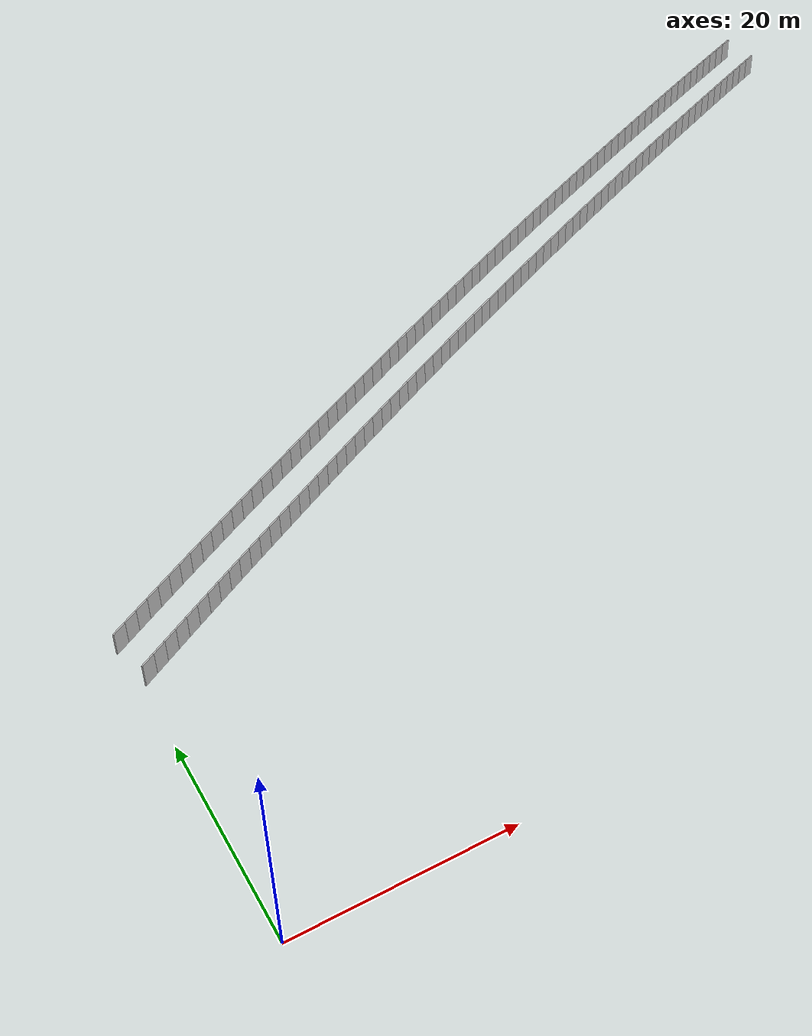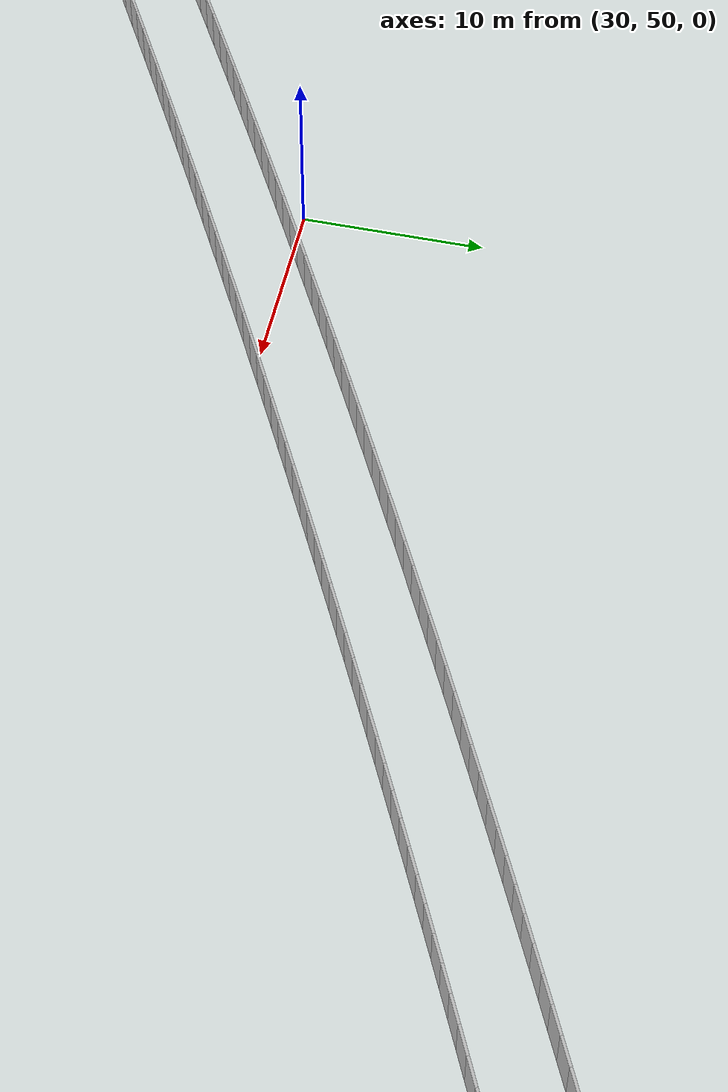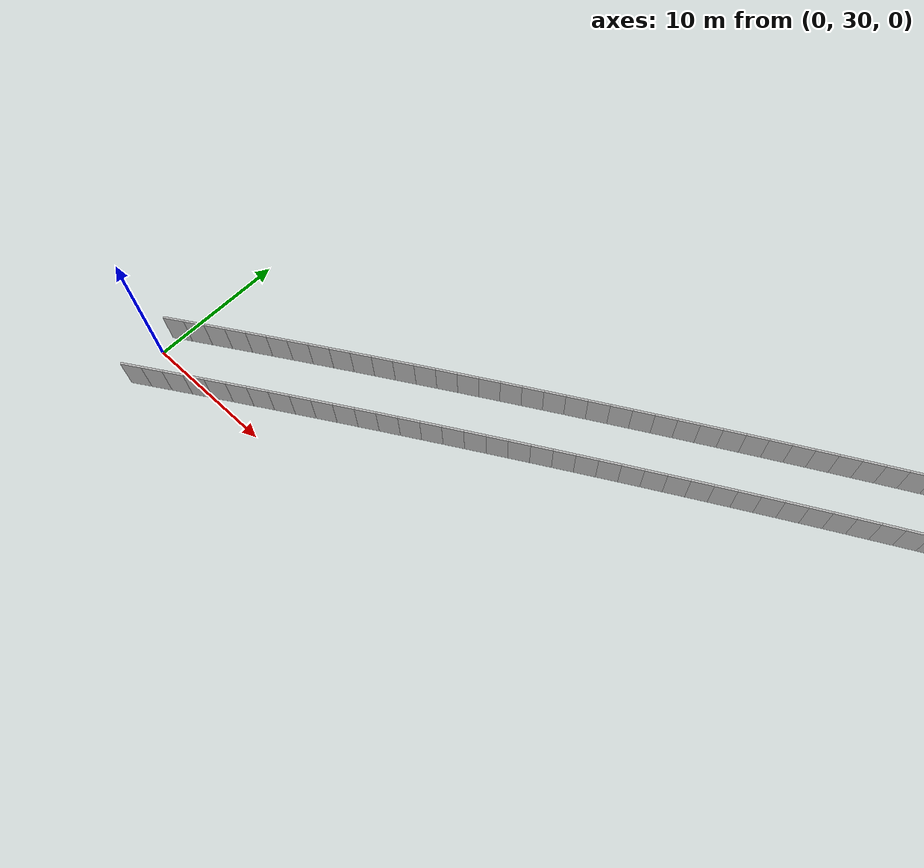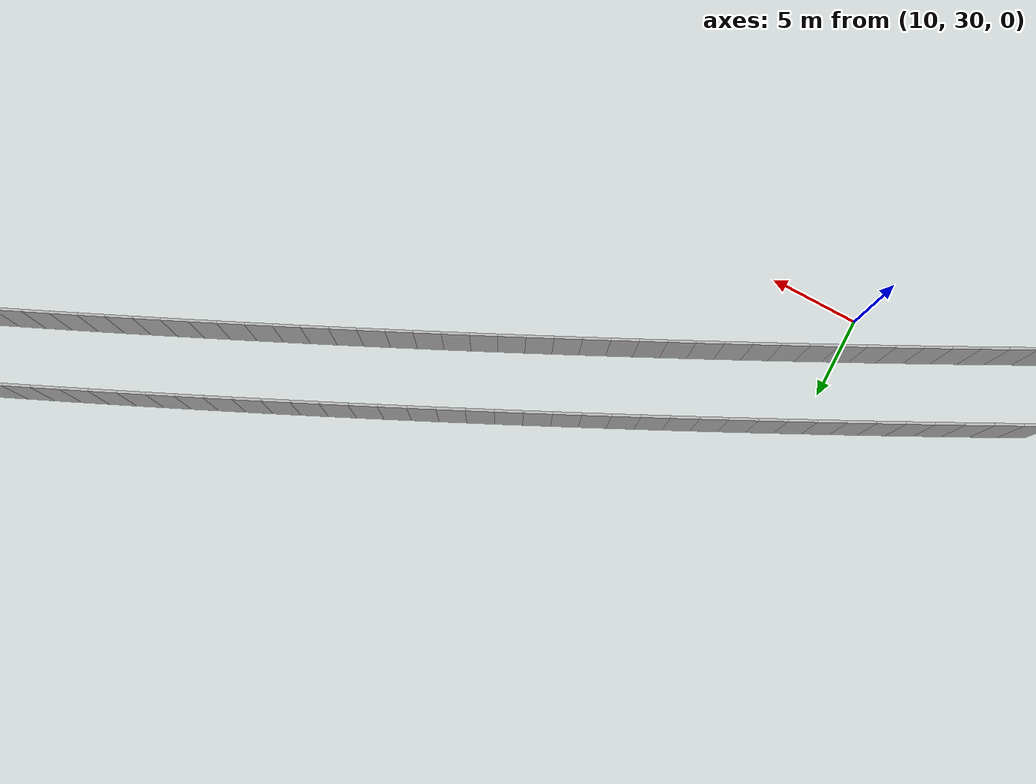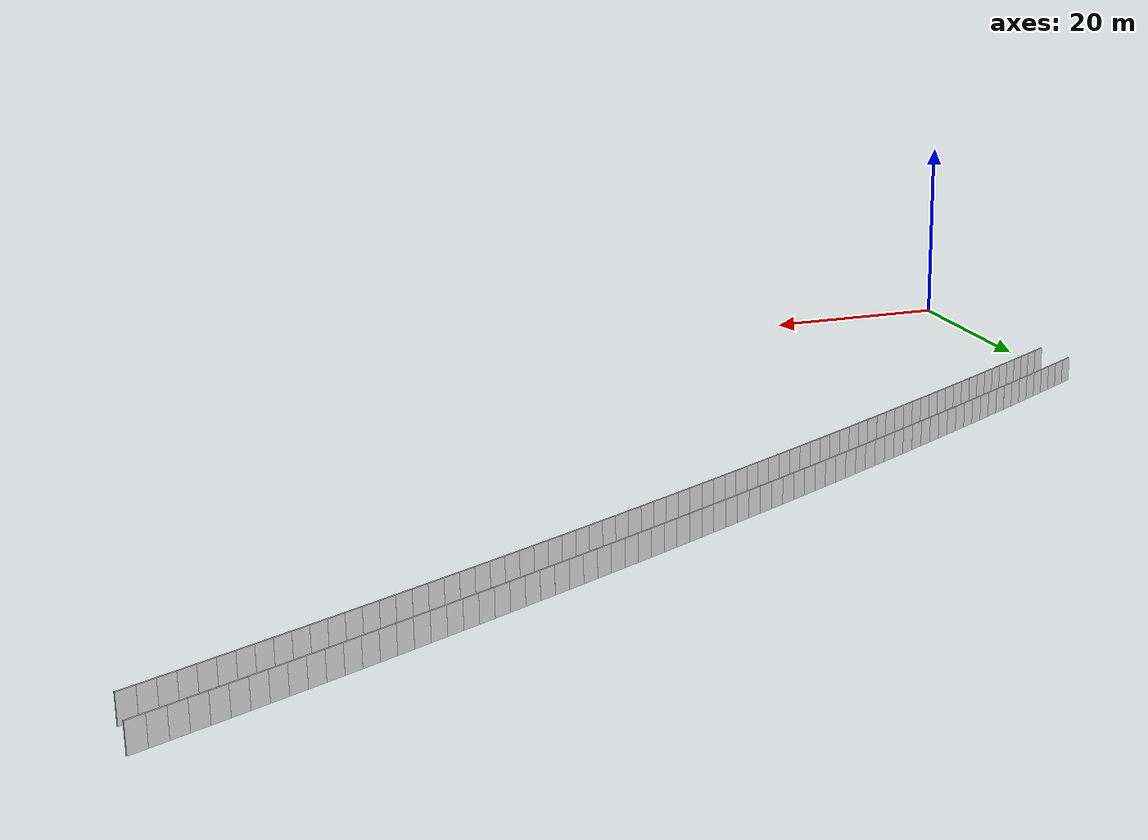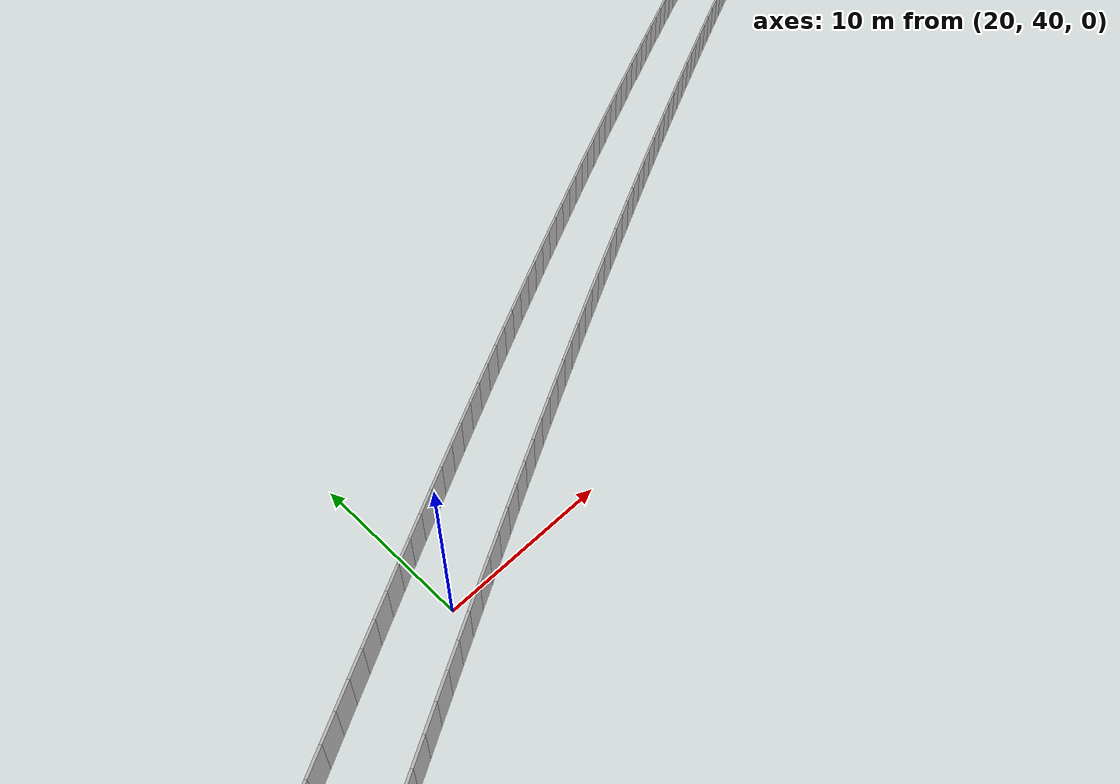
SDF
<?xml version="1.0" ?>
<sdf version="1.6">
  <model name="sps_0722">
    <pose frame="">0 0 0 0 -0 0</pose>
    <static>1</static>
    <self_collide>0</self_collide>
    <allow_auto_disable>0</allow_auto_disable>
    <link name="Wall3167">
      <kinematic>0</kinematic>
      <gravity>1</gravity>
      <self_collide>0</self_collide>
      <collision name="collision">
        <geometry>
          <box>
            <size>1.4966 0.15 2.5</size>
          </box>
        </geometry>
        <pose frame="">0 0 0 0 -0 0</pose>
      </collision>
      <visual name="visual">
        <geometry>
          <box>
            <size>1.4966 0.15 2.5</size>
          </box>
        </geometry>
        <pose frame="">0 0 0 0 -0 0</pose>
        <cast_shadows>1</cast_shadows>
        <transparency>0.0</transparency>
      </visual>
      <pose frame="">99.2956 78.1394 1.25 0 0 -2.72398</pose>
    </link>
    <link name="Wall3168">
      <kinematic>0</kinematic>
      <gravity>1</gravity>
      <self_collide>0</self_collide>
      <collision name="collision">
        <geometry>
          <box>
            <size>1.49636 0.15 2.5</size>
          </box>
        </geometry>
        <pose frame="">0 0 0 0 -0 0</pose>
      </collision>
      <visual name="visual">
        <geometry>
          <box>
            <size>1.49636 0.15 2.5</size>
          </box>
        </geometry>
        <pose frame="">0 0 0 0 -0 0</pose>
        <cast_shadows>1</cast_shadows>
        <transparency>0.0</transparency>
      </visual>
      <pose frame="">97.9282 77.5314 1.25 0 0 -2.72243</pose>
    </link>
    <link name="Wall3169">
      <kinematic>0</kinematic>
      <gravity>1</gravity>
      <self_collide>0</self_collide>
      <collision name="collision">
        <geometry>
          <box>
            <size>1.49648 0.15 2.5</size>
          </box>
        </geometry>
        <pose frame="">0 0 0 0 -0 0</pose>
      </collision>
      <visual name="visual">
        <geometry>
          <box>
            <size>1.49648 0.15 2.5</size>
          </box>
        </geometry>
        <pose frame="">0 0 0 0 -0 0</pose>
        <cast_shadows>1</cast_shadows>
        <transparency>0.0</transparency>
      </visual>
      <pose frame="">96.5619 76.9213 1.25 0 0 -2.72086</pose>
    </link>
    <link name="Wall3170">
      <kinematic>0</kinematic>
      <gravity>1</gravity>
      <self_collide>0</self_collide>
      <collision name="collision">
        <geometry>
          <box>
            <size>1.49656 0.15 2.5</size>
          </box>
        </geometry>
        <pose frame="">0 0 0 0 -0 0</pose>
      </collision>
      <visual name="visual">
        <geometry>
          <box>
            <size>1.49656 0.15 2.5</size>
          </box>
        </geometry>
        <pose frame="">0 0 0 0 -0 0</pose>
        <cast_shadows>1</cast_shadows>
        <transparency>0.0</transparency>
      </visual>
      <pose frame="">95.1964 76.3089 1.25 0 0 -2.71914</pose>
    </link>
    <link name="Wall3171">
      <kinematic>0</kinematic>
      <gravity>1</gravity>
      <self_collide>0</self_collide>
      <collision name="collision">
        <geometry>
          <box>
            <size>1.4965 0.15 2.5</size>
          </box>
        </geometry>
        <pose frame="">0 0 0 0 -0 0</pose>
      </collision>
      <visual name="visual">
        <geometry>
          <box>
            <size>1.4965 0.15 2.5</size>
          </box>
        </geometry>
        <pose frame="">0 0 0 0 -0 0</pose>
        <cast_shadows>1</cast_shadows>
        <transparency>0.0</transparency>
      </visual>
      <pose frame="">93.8319 75.6943 1.25 0 0 -2.71765</pose>
    </link>
    <link name="Wall3172">
      <kinematic>0</kinematic>
      <gravity>1</gravity>
      <self_collide>0</self_collide>
      <collision name="collision">
        <geometry>
          <box>
            <size>1.4966 0.15 2.5</size>
          </box>
        </geometry>
        <pose frame="">0 0 0 0 -0 0</pose>
      </collision>
      <visual name="visual">
        <geometry>
          <box>
            <size>1.4966 0.15 2.5</size>
          </box>
        </geometry>
        <pose frame="">0 0 0 0 -0 0</pose>
        <cast_shadows>1</cast_shadows>
        <transparency>0.0</transparency>
      </visual>
      <pose frame="">92.4683 75.0777 1.25 0 0 -2.7162</pose>
    </link>
    <link name="Wall3173">
      <kinematic>0</kinematic>
      <gravity>1</gravity>
      <self_collide>0</self_collide>
      <collision name="collision">
        <geometry>
          <box>
            <size>1.49647 0.15 2.5</size>
          </box>
        </geometry>
        <pose frame="">0 0 0 0 -0 0</pose>
      </collision>
      <visual name="visual">
        <geometry>
          <box>
            <size>1.49647 0.15 2.5</size>
          </box>
        </geometry>
        <pose frame="">0 0 0 0 -0 0</pose>
        <cast_shadows>1</cast_shadows>
        <transparency>0.0</transparency>
      </visual>
      <pose frame="">91.1056 74.4589 1.25 0 0 -2.71441</pose>
    </link>
    <link name="Wall3174">
      <kinematic>0</kinematic>
      <gravity>1</gravity>
      <self_collide>0</self_collide>
      <collision name="collision">
        <geometry>
          <box>
            <size>1.49659 0.15 2.5</size>
          </box>
        </geometry>
        <pose frame="">0 0 0 0 -0 0</pose>
      </collision>
      <visual name="visual">
        <geometry>
          <box>
            <size>1.49659 0.15 2.5</size>
          </box>
        </geometry>
        <pose frame="">0 0 0 0 -0 0</pose>
        <cast_shadows>1</cast_shadows>
        <transparency>0.0</transparency>
      </visual>
      <pose frame="">89.744 73.8379 1.25 0 0 -2.71297</pose>
    </link>
    <link name="Wall3175">
      <kinematic>0</kinematic>
      <gravity>1</gravity>
      <self_collide>0</self_collide>
      <collision name="collision">
        <geometry>
          <box>
            <size>1.49629 0.15 2.5</size>
          </box>
        </geometry>
        <pose frame="">0 0 0 0 -0 0</pose>
      </collision>
      <visual name="visual">
        <geometry>
          <box>
            <size>1.49629 0.15 2.5</size>
          </box>
        </geometry>
        <pose frame="">0 0 0 0 -0 0</pose>
        <cast_shadows>1</cast_shadows>
        <transparency>0.0</transparency>
      </visual>
      <pose frame="">88.3834 73.2149 1.25 0 0 -2.71144</pose>
    </link>
    <link name="Wall3176">
      <kinematic>0</kinematic>
      <gravity>1</gravity>
      <self_collide>0</self_collide>
      <collision name="collision">
        <geometry>
          <box>
            <size>1.49642 0.15 2.5</size>
          </box>
        </geometry>
        <pose frame="">0 0 0 0 -0 0</pose>
      </collision>
      <visual name="visual">
        <geometry>
          <box>
            <size>1.49642 0.15 2.5</size>
          </box>
        </geometry>
        <pose frame="">0 0 0 0 -0 0</pose>
        <cast_shadows>1</cast_shadows>
        <transparency>0.0</transparency>
      </visual>
      <pose frame="">87.0239 72.5897 1.25 0 0 -2.70969</pose>
    </link>
    <link name="Wall3177">
      <kinematic>0</kinematic>
      <gravity>1</gravity>
      <self_collide>0</self_collide>
      <collision name="collision">
        <geometry>
          <box>
            <size>1.49663 0.15 2.5</size>
          </box>
        </geometry>
        <pose frame="">0 0 0 0 -0 0</pose>
      </collision>
      <visual name="visual">
        <geometry>
          <box>
            <size>1.49663 0.15 2.5</size>
          </box>
        </geometry>
        <pose frame="">0 0 0 0 -0 0</pose>
        <cast_shadows>1</cast_shadows>
        <transparency>0.0</transparency>
      </visual>
      <pose frame="">85.6653 71.9622 1.25 0 0 -2.70813</pose>
    </link>
    <link name="Wall3178">
      <kinematic>0</kinematic>
      <gravity>1</gravity>
      <self_collide>0</self_collide>
      <collision name="collision">
        <geometry>
          <box>
            <size>1.49637 0.15 2.5</size>
          </box>
        </geometry>
        <pose frame="">0 0 0 0 -0 0</pose>
      </collision>
      <visual name="visual">
        <geometry>
          <box>
            <size>1.49637 0.15 2.5</size>
          </box>
        </geometry>
        <pose frame="">0 0 0 0 -0 0</pose>
        <cast_shadows>1</cast_shadows>
        <transparency>0.0</transparency>
      </visual>
      <pose frame="">84.3077 71.3326 1.25 0 0 -2.70657</pose>
    </link>
    <link name="Wall3179">
      <kinematic>0</kinematic>
      <gravity>1</gravity>
      <self_collide>0</self_collide>
      <collision name="collision">
        <geometry>
          <box>
            <size>1.49665 0.15 2.5</size>
          </box>
        </geometry>
        <pose frame="">0 0 0 0 -0 0</pose>
      </collision>
      <visual name="visual">
        <geometry>
          <box>
            <size>1.49665 0.15 2.5</size>
          </box>
        </geometry>
        <pose frame="">0 0 0 0 -0 0</pose>
        <cast_shadows>1</cast_shadows>
        <transparency>0.0</transparency>
      </visual>
      <pose frame="">82.9511 70.7008 1.25 0 0 -2.7049</pose>
    </link>
    <link name="Wall3180">
      <kinematic>0</kinematic>
      <gravity>1</gravity>
      <self_collide>0</self_collide>
      <collision name="collision">
        <geometry>
          <box>
            <size>1.4964 0.15 2.5</size>
          </box>
        </geometry>
        <pose frame="">0 0 0 0 -0 0</pose>
      </collision>
      <visual name="visual">
        <geometry>
          <box>
            <size>1.4964 0.15 2.5</size>
          </box>
        </geometry>
        <pose frame="">0 0 0 0 -0 0</pose>
        <cast_shadows>1</cast_shadows>
        <transparency>0.0</transparency>
      </visual>
      <pose frame="">81.5955 70.0668 1.25 0 0 -2.70334</pose>
    </link>
    <link name="Wall3181">
      <kinematic>0</kinematic>
      <gravity>1</gravity>
      <self_collide>0</self_collide>
      <collision name="collision">
        <geometry>
          <box>
            <size>1.49661 0.15 2.5</size>
          </box>
        </geometry>
        <pose frame="">0 0 0 0 -0 0</pose>
      </collision>
      <visual name="visual">
        <geometry>
          <box>
            <size>1.49661 0.15 2.5</size>
          </box>
        </geometry>
        <pose frame="">0 0 0 0 -0 0</pose>
        <cast_shadows>1</cast_shadows>
        <transparency>0.0</transparency>
      </visual>
      <pose frame="">80.241 69.4307 1.25 0 0 -2.70178</pose>
    </link>
    <link name="Wall3182">
      <kinematic>0</kinematic>
      <gravity>1</gravity>
      <self_collide>0</self_collide>
      <collision name="collision">
        <geometry>
          <box>
            <size>1.4964 0.15 2.5</size>
          </box>
        </geometry>
        <pose frame="">0 0 0 0 -0 0</pose>
      </collision>
      <visual name="visual">
        <geometry>
          <box>
            <size>1.4964 0.15 2.5</size>
          </box>
        </geometry>
        <pose frame="">0 0 0 0 -0 0</pose>
        <cast_shadows>1</cast_shadows>
        <transparency>0.0</transparency>
      </visual>
      <pose frame="">78.8874 68.7925 1.25 0 0 -2.70027</pose>
    </link>
    <link name="Wall3183">
      <kinematic>0</kinematic>
      <gravity>1</gravity>
      <self_collide>0</self_collide>
      <collision name="collision">
        <geometry>
          <box>
            <size>1.49635 0.15 2.5</size>
          </box>
        </geometry>
        <pose frame="">0 0 0 0 -0 0</pose>
      </collision>
      <visual name="visual">
        <geometry>
          <box>
            <size>1.49635 0.15 2.5</size>
          </box>
        </geometry>
        <pose frame="">0 0 0 0 -0 0</pose>
        <cast_shadows>1</cast_shadows>
        <transparency>0.0</transparency>
      </visual>
      <pose frame="">77.5348 68.1523 1.25 0 0 -2.69872</pose>
    </link>
    <link name="Wall3184">
      <kinematic>0</kinematic>
      <gravity>1</gravity>
      <self_collide>0</self_collide>
      <collision name="collision">
        <geometry>
          <box>
            <size>1.49665 0.15 2.5</size>
          </box>
        </geometry>
        <pose frame="">0 0 0 0 -0 0</pose>
      </collision>
      <visual name="visual">
        <geometry>
          <box>
            <size>1.49665 0.15 2.5</size>
          </box>
        </geometry>
        <pose frame="">0 0 0 0 -0 0</pose>
        <cast_shadows>1</cast_shadows>
        <transparency>0.0</transparency>
      </visual>
      <pose frame="">76.1832 67.5099 1.25 0 0 -2.69706</pose>
    </link>
    <link name="Wall3185">
      <kinematic>0</kinematic>
      <gravity>1</gravity>
      <self_collide>0</self_collide>
      <collision name="collision">
        <geometry>
          <box>
            <size>1.49639 0.15 2.5</size>
          </box>
        </geometry>
        <pose frame="">0 0 0 0 -0 0</pose>
      </collision>
      <visual name="visual">
        <geometry>
          <box>
            <size>1.49639 0.15 2.5</size>
          </box>
        </geometry>
        <pose frame="">0 0 0 0 -0 0</pose>
        <cast_shadows>1</cast_shadows>
        <transparency>0.0</transparency>
      </visual>
      <pose frame="">74.8327 66.8653 1.25 0 0 -2.69553</pose>
    </link>
    <link name="Wall3186">
      <kinematic>0</kinematic>
      <gravity>1</gravity>
      <self_collide>0</self_collide>
      <collision name="collision">
        <geometry>
          <box>
            <size>1.49649 0.15 2.5</size>
          </box>
        </geometry>
        <pose frame="">0 0 0 0 -0 0</pose>
      </collision>
      <visual name="visual">
        <geometry>
          <box>
            <size>1.49649 0.15 2.5</size>
          </box>
        </geometry>
        <pose frame="">0 0 0 0 -0 0</pose>
        <cast_shadows>1</cast_shadows>
        <transparency>0.0</transparency>
      </visual>
      <pose frame="">73.4832 66.2186 1.25 0 0 -2.69389</pose>
    </link>
    <link name="Wall3187">
      <kinematic>0</kinematic>
      <gravity>1</gravity>
      <self_collide>0</self_collide>
      <collision name="collision">
        <geometry>
          <box>
            <size>1.49653 0.15 2.5</size>
          </box>
        </geometry>
        <pose frame="">0 0 0 0 -0 0</pose>
      </collision>
      <visual name="visual">
        <geometry>
          <box>
            <size>1.49653 0.15 2.5</size>
          </box>
        </geometry>
        <pose frame="">0 0 0 0 -0 0</pose>
        <cast_shadows>1</cast_shadows>
        <transparency>0.0</transparency>
      </visual>
      <pose frame="">72.1347 65.5697 1.25 0 0 -2.69232</pose>
    </link>
    <link name="Wall3188">
      <kinematic>0</kinematic>
      <gravity>1</gravity>
      <self_collide>0</self_collide>
      <collision name="collision">
        <geometry>
          <box>
            <size>1.49658 0.15 2.5</size>
          </box>
        </geometry>
        <pose frame="">0 0 0 0 -0 0</pose>
      </collision>
      <visual name="visual">
        <geometry>
          <box>
            <size>1.49658 0.15 2.5</size>
          </box>
        </geometry>
        <pose frame="">0 0 0 0 -0 0</pose>
        <cast_shadows>1</cast_shadows>
        <transparency>0.0</transparency>
      </visual>
      <pose frame="">70.7872 64.9186 1.25 0 0 -2.69066</pose>
    </link>
    <link name="Wall3189">
      <kinematic>0</kinematic>
      <gravity>1</gravity>
      <self_collide>0</self_collide>
      <collision name="collision">
        <geometry>
          <box>
            <size>1.49666 0.15 2.5</size>
          </box>
        </geometry>
        <pose frame="">0 0 0 0 -0 0</pose>
      </collision>
      <visual name="visual">
        <geometry>
          <box>
            <size>1.49666 0.15 2.5</size>
          </box>
        </geometry>
        <pose frame="">0 0 0 0 -0 0</pose>
        <cast_shadows>1</cast_shadows>
        <transparency>0.0</transparency>
      </visual>
      <pose frame="">69.4407 64.2653 1.25 0 0 -2.68905</pose>
    </link>
    <link name="Wall3190">
      <kinematic>0</kinematic>
      <gravity>1</gravity>
      <self_collide>0</self_collide>
      <collision name="collision">
        <geometry>
          <box>
            <size>1.49634 0.15 2.5</size>
          </box>
        </geometry>
        <pose frame="">0 0 0 0 -0 0</pose>
      </collision>
      <visual name="visual">
        <geometry>
          <box>
            <size>1.49634 0.15 2.5</size>
          </box>
        </geometry>
        <pose frame="">0 0 0 0 -0 0</pose>
        <cast_shadows>1</cast_shadows>
        <transparency>0.0</transparency>
      </visual>
      <pose frame="">68.0953 63.61 1.25 0 0 -2.68763</pose>
    </link>
    <link name="Wall3191">
      <kinematic>0</kinematic>
      <gravity>1</gravity>
      <self_collide>0</self_collide>
      <collision name="collision">
        <geometry>
          <box>
            <size>1.49651 0.15 2.5</size>
          </box>
        </geometry>
        <pose frame="">0 0 0 0 -0 0</pose>
      </collision>
      <visual name="visual">
        <geometry>
          <box>
            <size>1.49651 0.15 2.5</size>
          </box>
        </geometry>
        <pose frame="">0 0 0 0 -0 0</pose>
        <cast_shadows>1</cast_shadows>
        <transparency>0.0</transparency>
      </visual>
      <pose frame="">66.751 62.9526 1.25 0 0 -2.68592</pose>
    </link>
    <link name="Wall3192">
      <kinematic>0</kinematic>
      <gravity>1</gravity>
      <self_collide>0</self_collide>
      <collision name="collision">
        <geometry>
          <box>
            <size>1.49622 0.15 2.5</size>
          </box>
        </geometry>
        <pose frame="">0 0 0 0 -0 0</pose>
      </collision>
      <visual name="visual">
        <geometry>
          <box>
            <size>1.49622 0.15 2.5</size>
          </box>
        </geometry>
        <pose frame="">0 0 0 0 -0 0</pose>
        <cast_shadows>1</cast_shadows>
        <transparency>0.0</transparency>
      </visual>
      <pose frame="">65.4078 62.2931 1.25 0 0 -2.68446</pose>
    </link>
    <link name="Wall3193">
      <kinematic>0</kinematic>
      <gravity>1</gravity>
      <self_collide>0</self_collide>
      <collision name="collision">
        <geometry>
          <box>
            <size>1.49659 0.15 2.5</size>
          </box>
        </geometry>
        <pose frame="">0 0 0 0 -0 0</pose>
      </collision>
      <visual name="visual">
        <geometry>
          <box>
            <size>1.49659 0.15 2.5</size>
          </box>
        </geometry>
        <pose frame="">0 0 0 0 -0 0</pose>
        <cast_shadows>1</cast_shadows>
        <transparency>0.0</transparency>
      </visual>
      <pose frame="">64.0656 61.6315 1.25 0 0 -2.68276</pose>
    </link>
    <link name="Wall3194">
      <kinematic>0</kinematic>
      <gravity>1</gravity>
      <self_collide>0</self_collide>
      <collision name="collision">
        <geometry>
          <box>
            <size>1.49658 0.15 2.5</size>
          </box>
        </geometry>
        <pose frame="">0 0 0 0 -0 0</pose>
      </collision>
      <visual name="visual">
        <geometry>
          <box>
            <size>1.49658 0.15 2.5</size>
          </box>
        </geometry>
        <pose frame="">0 0 0 0 -0 0</pose>
        <cast_shadows>1</cast_shadows>
        <transparency>0.0</transparency>
      </visual>
      <pose frame="">62.7243 60.9677 1.25 0 0 -2.6813</pose>
    </link>
    <link name="Wall3195">
      <kinematic>0</kinematic>
      <gravity>1</gravity>
      <self_collide>0</self_collide>
      <collision name="collision">
        <geometry>
          <box>
            <size>1.49663 0.15 2.5</size>
          </box>
        </geometry>
        <pose frame="">0 0 0 0 -0 0</pose>
      </collision>
      <visual name="visual">
        <geometry>
          <box>
            <size>1.49663 0.15 2.5</size>
          </box>
        </geometry>
        <pose frame="">0 0 0 0 -0 0</pose>
        <cast_shadows>1</cast_shadows>
        <transparency>0.0</transparency>
      </visual>
      <pose frame="">61.384 60.3018 1.25 0 0 -2.67968</pose>
    </link>
    <link name="Wall3196">
      <kinematic>0</kinematic>
      <gravity>1</gravity>
      <self_collide>0</self_collide>
      <collision name="collision">
        <geometry>
          <box>
            <size>1.49641 0.15 2.5</size>
          </box>
        </geometry>
        <pose frame="">0 0 0 0 -0 0</pose>
      </collision>
      <visual name="visual">
        <geometry>
          <box>
            <size>1.49641 0.15 2.5</size>
          </box>
        </geometry>
        <pose frame="">0 0 0 0 -0 0</pose>
        <cast_shadows>1</cast_shadows>
        <transparency>0.0</transparency>
      </visual>
      <pose frame="">60.0449 59.6337 1.25 0 0 -2.67796</pose>
    </link>
    <link name="Wall3197">
      <kinematic>0</kinematic>
      <gravity>1</gravity>
      <self_collide>0</self_collide>
      <collision name="collision">
        <geometry>
          <box>
            <size>1.49655 0.15 2.5</size>
          </box>
        </geometry>
        <pose frame="">0 0 0 0 -0 0</pose>
      </collision>
      <visual name="visual">
        <geometry>
          <box>
            <size>1.49655 0.15 2.5</size>
          </box>
        </geometry>
        <pose frame="">0 0 0 0 -0 0</pose>
        <cast_shadows>1</cast_shadows>
        <transparency>0.0</transparency>
      </visual>
      <pose frame="">58.7068 58.9635 1.25 0 0 -2.6765</pose>
    </link>
    <link name="Wall3198">
      <kinematic>0</kinematic>
      <gravity>1</gravity>
      <self_collide>0</self_collide>
      <collision name="collision">
        <geometry>
          <box>
            <size>1.49644 0.15 2.5</size>
          </box>
        </geometry>
        <pose frame="">0 0 0 0 -0 0</pose>
      </collision>
      <visual name="visual">
        <geometry>
          <box>
            <size>1.49644 0.15 2.5</size>
          </box>
        </geometry>
        <pose frame="">0 0 0 0 -0 0</pose>
        <cast_shadows>1</cast_shadows>
        <transparency>0.0</transparency>
      </visual>
      <pose frame="">57.3699 58.2912 1.25 0 0 -2.67483</pose>
    </link>
    <link name="Wall3199">
      <kinematic>0</kinematic>
      <gravity>1</gravity>
      <self_collide>0</self_collide>
      <collision name="collision">
        <geometry>
          <box>
            <size>1.49653 0.15 2.5</size>
          </box>
        </geometry>
        <pose frame="">0 0 0 0 -0 0</pose>
      </collision>
      <visual name="visual">
        <geometry>
          <box>
            <size>1.49653 0.15 2.5</size>
          </box>
        </geometry>
        <pose frame="">0 0 0 0 -0 0</pose>
        <cast_shadows>1</cast_shadows>
        <transparency>0.0</transparency>
      </visual>
      <pose frame="">56.034 57.6168 1.25 0 0 -2.67335</pose>
    </link>
    <link name="Wall3200">
      <kinematic>0</kinematic>
      <gravity>1</gravity>
      <self_collide>0</self_collide>
      <collision name="collision">
        <geometry>
          <box>
            <size>1.49652 0.15 2.5</size>
          </box>
        </geometry>
        <pose frame="">0 0 0 0 -0 0</pose>
      </collision>
      <visual name="visual">
        <geometry>
          <box>
            <size>1.49652 0.15 2.5</size>
          </box>
        </geometry>
        <pose frame="">0 0 0 0 -0 0</pose>
        <cast_shadows>1</cast_shadows>
        <transparency>0.0</transparency>
      </visual>
      <pose frame="">54.6991 56.9403 1.25 0 0 -2.67174</pose>
    </link>
    <link name="Wall3201">
      <kinematic>0</kinematic>
      <gravity>1</gravity>
      <self_collide>0</self_collide>
      <collision name="collision">
        <geometry>
          <box>
            <size>1.49656 0.15 2.5</size>
          </box>
        </geometry>
        <pose frame="">0 0 0 0 -0 0</pose>
      </collision>
      <visual name="visual">
        <geometry>
          <box>
            <size>1.49656 0.15 2.5</size>
          </box>
        </geometry>
        <pose frame="">0 0 0 0 -0 0</pose>
        <cast_shadows>1</cast_shadows>
        <transparency>0.0</transparency>
      </visual>
      <pose frame="">53.3653 56.2616 1.25 0 0 -2.67007</pose>
    </link>
    <link name="Wall3202">
      <kinematic>0</kinematic>
      <gravity>1</gravity>
      <self_collide>0</self_collide>
      <collision name="collision">
        <geometry>
          <box>
            <size>1.4965 0.15 2.5</size>
          </box>
        </geometry>
        <pose frame="">0 0 0 0 -0 0</pose>
      </collision>
      <visual name="visual">
        <geometry>
          <box>
            <size>1.4965 0.15 2.5</size>
          </box>
        </geometry>
        <pose frame="">0 0 0 0 -0 0</pose>
        <cast_shadows>1</cast_shadows>
        <transparency>0.0</transparency>
      </visual>
      <pose frame="">52.0326 55.5808 1.25 0 0 -2.66853</pose>
    </link>
    <link name="Wall3203">
      <kinematic>0</kinematic>
      <gravity>1</gravity>
      <self_collide>0</self_collide>
      <collision name="collision">
        <geometry>
          <box>
            <size>1.49644 0.15 2.5</size>
          </box>
        </geometry>
        <pose frame="">0 0 0 0 -0 0</pose>
      </collision>
      <visual name="visual">
        <geometry>
          <box>
            <size>1.49644 0.15 2.5</size>
          </box>
        </geometry>
        <pose frame="">0 0 0 0 -0 0</pose>
        <cast_shadows>1</cast_shadows>
        <transparency>0.0</transparency>
      </visual>
      <pose frame="">50.701 54.8979 1.25 0 0 -2.66691</pose>
    </link>
    <link name="Wall3204">
      <kinematic>0</kinematic>
      <gravity>1</gravity>
      <self_collide>0</self_collide>
      <collision name="collision">
        <geometry>
          <box>
            <size>1.49653 0.15 2.5</size>
          </box>
        </geometry>
        <pose frame="">0 0 0 0 -0 0</pose>
      </collision>
      <visual name="visual">
        <geometry>
          <box>
            <size>1.49653 0.15 2.5</size>
          </box>
        </geometry>
        <pose frame="">0 0 0 0 -0 0</pose>
        <cast_shadows>1</cast_shadows>
        <transparency>0.0</transparency>
      </visual>
      <pose frame="">49.3705 54.2129 1.25 0 0 -2.66538</pose>
    </link>
    <link name="Wall3205">
      <kinematic>0</kinematic>
      <gravity>1</gravity>
      <self_collide>0</self_collide>
      <collision name="collision">
        <geometry>
          <box>
            <size>1.49642 0.15 2.5</size>
          </box>
        </geometry>
        <pose frame="">0 0 0 0 -0 0</pose>
      </collision>
      <visual name="visual">
        <geometry>
          <box>
            <size>1.49642 0.15 2.5</size>
          </box>
        </geometry>
        <pose frame="">0 0 0 0 -0 0</pose>
        <cast_shadows>1</cast_shadows>
        <transparency>0.0</transparency>
      </visual>
      <pose frame="">48.0411 53.5258 1.25 0 0 -2.66374</pose>
    </link>
    <link name="Wall3206">
      <kinematic>0</kinematic>
      <gravity>1</gravity>
      <self_collide>0</self_collide>
      <collision name="collision">
        <geometry>
          <box>
            <size>1.49651 0.15 2.5</size>
          </box>
        </geometry>
        <pose frame="">0 0 0 0 -0 0</pose>
      </collision>
      <visual name="visual">
        <geometry>
          <box>
            <size>1.49651 0.15 2.5</size>
          </box>
        </geometry>
        <pose frame="">0 0 0 0 -0 0</pose>
        <cast_shadows>1</cast_shadows>
        <transparency>0.0</transparency>
      </visual>
      <pose frame="">46.7128 52.8366 1.25 0 0 -2.6622</pose>
    </link>
    <link name="Wall3207">
      <kinematic>0</kinematic>
      <gravity>1</gravity>
      <self_collide>0</self_collide>
      <collision name="collision">
        <geometry>
          <box>
            <size>1.49649 0.15 2.5</size>
          </box>
        </geometry>
        <pose frame="">0 0 0 0 -0 0</pose>
      </collision>
      <visual name="visual">
        <geometry>
          <box>
            <size>1.49649 0.15 2.5</size>
          </box>
        </geometry>
        <pose frame="">0 0 0 0 -0 0</pose>
        <cast_shadows>1</cast_shadows>
        <transparency>0.0</transparency>
      </visual>
      <pose frame="">45.3855 52.1454 1.25 0 0 -2.66073</pose>
    </link>
    <link name="Wall3208">
      <kinematic>0</kinematic>
      <gravity>1</gravity>
      <self_collide>0</self_collide>
      <collision name="collision">
        <geometry>
          <box>
            <size>1.49657 0.15 2.5</size>
          </box>
        </geometry>
        <pose frame="">0 0 0 0 -0 0</pose>
      </collision>
      <visual name="visual">
        <geometry>
          <box>
            <size>1.49657 0.15 2.5</size>
          </box>
        </geometry>
        <pose frame="">0 0 0 0 -0 0</pose>
        <cast_shadows>1</cast_shadows>
        <transparency>0.0</transparency>
      </visual>
      <pose frame="">44.0593 51.452 1.25 0 0 -2.65896</pose>
    </link>
    <link name="Wall3209">
      <kinematic>0</kinematic>
      <gravity>1</gravity>
      <self_collide>0</self_collide>
      <collision name="collision">
        <geometry>
          <box>
            <size>1.49622 0.15 2.5</size>
          </box>
        </geometry>
        <pose frame="">0 0 0 0 -0 0</pose>
      </collision>
      <visual name="visual">
        <geometry>
          <box>
            <size>1.49622 0.15 2.5</size>
          </box>
        </geometry>
        <pose frame="">0 0 0 0 -0 0</pose>
        <cast_shadows>1</cast_shadows>
        <transparency>0.0</transparency>
      </visual>
      <pose frame="">42.7342 50.7566 1.25 0 0 -2.65764</pose>
    </link>
    <link name="Wall3210">
      <kinematic>0</kinematic>
      <gravity>1</gravity>
      <self_collide>0</self_collide>
      <collision name="collision">
        <geometry>
          <box>
            <size>1.49677 0.15 2.5</size>
          </box>
        </geometry>
        <pose frame="">0 0 0 0 -0 0</pose>
      </collision>
      <visual name="visual">
        <geometry>
          <box>
            <size>1.49677 0.15 2.5</size>
          </box>
        </geometry>
        <pose frame="">0 0 0 0 -0 0</pose>
        <cast_shadows>1</cast_shadows>
        <transparency>0.0</transparency>
      </visual>
      <pose frame="">41.4102 50.0591 1.25 0 0 -2.6558</pose>
    </link>
    <link name="Wall3211">
      <kinematic>0</kinematic>
      <gravity>1</gravity>
      <self_collide>0</self_collide>
      <collision name="collision">
        <geometry>
          <box>
            <size>1.49633 0.15 2.5</size>
          </box>
        </geometry>
        <pose frame="">0 0 0 0 -0 0</pose>
      </collision>
      <visual name="visual">
        <geometry>
          <box>
            <size>1.49633 0.15 2.5</size>
          </box>
        </geometry>
        <pose frame="">0 0 0 0 -0 0</pose>
        <cast_shadows>1</cast_shadows>
        <transparency>0.0</transparency>
      </visual>
      <pose frame="">40.0873 49.3594 1.25 0 0 -2.65436</pose>
    </link>
    <link name="Wall3212">
      <kinematic>0</kinematic>
      <gravity>1</gravity>
      <self_collide>0</self_collide>
      <collision name="collision">
        <geometry>
          <box>
            <size>1.49648 0.15 2.5</size>
          </box>
        </geometry>
        <pose frame="">0 0 0 0 -0 0</pose>
      </collision>
      <visual name="visual">
        <geometry>
          <box>
            <size>1.49648 0.15 2.5</size>
          </box>
        </geometry>
        <pose frame="">0 0 0 0 -0 0</pose>
        <cast_shadows>1</cast_shadows>
        <transparency>0.0</transparency>
      </visual>
      <pose frame="">38.7656 48.6577 1.25 0 0 -2.6527</pose>
    </link>
    <link name="Wall3213">
      <kinematic>0</kinematic>
      <gravity>1</gravity>
      <self_collide>0</self_collide>
      <collision name="collision">
        <geometry>
          <box>
            <size>1.49649 0.15 2.5</size>
          </box>
        </geometry>
        <pose frame="">0 0 0 0 -0 0</pose>
      </collision>
      <visual name="visual">
        <geometry>
          <box>
            <size>1.49649 0.15 2.5</size>
          </box>
        </geometry>
        <pose frame="">0 0 0 0 -0 0</pose>
        <cast_shadows>1</cast_shadows>
        <transparency>0.0</transparency>
      </visual>
      <pose frame="">37.4451 47.9538 1.25 0 0 -2.65104</pose>
    </link>
    <link name="Wall3214">
      <kinematic>0</kinematic>
      <gravity>1</gravity>
      <self_collide>0</self_collide>
      <collision name="collision">
        <geometry>
          <box>
            <size>1.49663 0.15 2.5</size>
          </box>
        </geometry>
        <pose frame="">0 0 0 0 -0 0</pose>
      </collision>
      <visual name="visual">
        <geometry>
          <box>
            <size>1.49663 0.15 2.5</size>
          </box>
        </geometry>
        <pose frame="">0 0 0 0 -0 0</pose>
        <cast_shadows>1</cast_shadows>
        <transparency>0.0</transparency>
      </visual>
      <pose frame="">36.1255 47.2477 1.25 0 0 -2.64947</pose>
    </link>
    <link name="Wall3215">
      <kinematic>0</kinematic>
      <gravity>1</gravity>
      <self_collide>0</self_collide>
      <collision name="collision">
        <geometry>
          <box>
            <size>1.4964 0.15 2.5</size>
          </box>
        </geometry>
        <pose frame="">0 0 0 0 -0 0</pose>
      </collision>
      <visual name="visual">
        <geometry>
          <box>
            <size>1.4964 0.15 2.5</size>
          </box>
        </geometry>
        <pose frame="">0 0 0 0 -0 0</pose>
        <cast_shadows>1</cast_shadows>
        <transparency>0.0</transparency>
      </visual>
      <pose frame="">34.8072 46.5396 1.25 0 0 -2.64795</pose>
    </link>
    <link name="Wall3216">
      <kinematic>0</kinematic>
      <gravity>1</gravity>
      <self_collide>0</self_collide>
      <collision name="collision">
        <geometry>
          <box>
            <size>1.49644 0.15 2.5</size>
          </box>
        </geometry>
        <pose frame="">0 0 0 0 -0 0</pose>
      </collision>
      <visual name="visual">
        <geometry>
          <box>
            <size>1.49644 0.15 2.5</size>
          </box>
        </geometry>
        <pose frame="">0 0 0 0 -0 0</pose>
        <cast_shadows>1</cast_shadows>
        <transparency>0.0</transparency>
      </visual>
      <pose frame="">33.49 45.8295 1.25 0 0 -2.64635</pose>
    </link>
    <link name="Wall3217">
      <kinematic>0</kinematic>
      <gravity>1</gravity>
      <self_collide>0</self_collide>
      <collision name="collision">
        <geometry>
          <box>
            <size>1.49652 0.15 2.5</size>
          </box>
        </geometry>
        <pose frame="">0 0 0 0 -0 0</pose>
      </collision>
      <visual name="visual">
        <geometry>
          <box>
            <size>1.49652 0.15 2.5</size>
          </box>
        </geometry>
        <pose frame="">0 0 0 0 -0 0</pose>
        <cast_shadows>1</cast_shadows>
        <transparency>0.0</transparency>
      </visual>
      <pose frame="">32.1739 45.1172 1.25 0 0 -2.64471</pose>
    </link>
    <link name="Wall3218">
      <kinematic>0</kinematic>
      <gravity>1</gravity>
      <self_collide>0</self_collide>
      <collision name="collision">
        <geometry>
          <box>
            <size>1.49668 0.15 2.5</size>
          </box>
        </geometry>
        <pose frame="">0 0 0 0 -0 0</pose>
      </collision>
      <visual name="visual">
        <geometry>
          <box>
            <size>1.49668 0.15 2.5</size>
          </box>
        </geometry>
        <pose frame="">0 0 0 0 -0 0</pose>
        <cast_shadows>1</cast_shadows>
        <transparency>0.0</transparency>
      </visual>
      <pose frame="">30.8588 44.4028 1.25 0 0 -2.64323</pose>
    </link>
    <link name="Wall3219">
      <kinematic>0</kinematic>
      <gravity>1</gravity>
      <self_collide>0</self_collide>
      <collision name="collision">
        <geometry>
          <box>
            <size>1.49636 0.15 2.5</size>
          </box>
        </geometry>
        <pose frame="">0 0 0 0 -0 0</pose>
      </collision>
      <visual name="visual">
        <geometry>
          <box>
            <size>1.49636 0.15 2.5</size>
          </box>
        </geometry>
        <pose frame="">0 0 0 0 -0 0</pose>
        <cast_shadows>1</cast_shadows>
        <transparency>0.0</transparency>
      </visual>
      <pose frame="">29.5449 43.6864 1.25 0 0 -2.64158</pose>
    </link>
    <link name="Wall3220">
      <kinematic>0</kinematic>
      <gravity>1</gravity>
      <self_collide>0</self_collide>
      <collision name="collision">
        <geometry>
          <box>
            <size>1.49647 0.15 2.5</size>
          </box>
        </geometry>
        <pose frame="">0 0 0 0 -0 0</pose>
      </collision>
      <visual name="visual">
        <geometry>
          <box>
            <size>1.49647 0.15 2.5</size>
          </box>
        </geometry>
        <pose frame="">0 0 0 0 -0 0</pose>
        <cast_shadows>1</cast_shadows>
        <transparency>0.0</transparency>
      </visual>
      <pose frame="">28.2322 42.968 1.25 0 0 -2.64009</pose>
    </link>
    <link name="Wall3221">
      <kinematic>0</kinematic>
      <gravity>1</gravity>
      <self_collide>0</self_collide>
      <collision name="collision">
        <geometry>
          <box>
            <size>1.4966 0.15 2.5</size>
          </box>
        </geometry>
        <pose frame="">0 0 0 0 -0 0</pose>
      </collision>
      <visual name="visual">
        <geometry>
          <box>
            <size>1.4966 0.15 2.5</size>
          </box>
        </geometry>
        <pose frame="">0 0 0 0 -0 0</pose>
        <cast_shadows>1</cast_shadows>
        <transparency>0.0</transparency>
      </visual>
      <pose frame="">26.9206 42.2474 1.25 0 0 -2.63832</pose>
    </link>
    <link name="Wall3222">
      <kinematic>0</kinematic>
      <gravity>1</gravity>
      <self_collide>0</self_collide>
      <collision name="collision">
        <geometry>
          <box>
            <size>1.49633 0.15 2.5</size>
          </box>
        </geometry>
        <pose frame="">0 0 0 0 -0 0</pose>
      </collision>
      <visual name="visual">
        <geometry>
          <box>
            <size>1.49633 0.15 2.5</size>
          </box>
        </geometry>
        <pose frame="">0 0 0 0 -0 0</pose>
        <cast_shadows>1</cast_shadows>
        <transparency>0.0</transparency>
      </visual>
      <pose frame="">25.6102 41.5247 1.25 0 0 -2.63687</pose>
    </link>
    <link name="Wall3223">
      <kinematic>0</kinematic>
      <gravity>1</gravity>
      <self_collide>0</self_collide>
      <collision name="collision">
        <geometry>
          <box>
            <size>1.49662 0.15 2.5</size>
          </box>
        </geometry>
        <pose frame="">0 0 0 0 -0 0</pose>
      </collision>
      <visual name="visual">
        <geometry>
          <box>
            <size>1.49662 0.15 2.5</size>
          </box>
        </geometry>
        <pose frame="">0 0 0 0 -0 0</pose>
        <cast_shadows>1</cast_shadows>
        <transparency>0.0</transparency>
      </visual>
      <pose frame="">24.3009 40.8 1.25 0 0 -2.63525</pose>
    </link>
    <link name="Wall3224">
      <kinematic>0</kinematic>
      <gravity>1</gravity>
      <self_collide>0</self_collide>
      <collision name="collision">
        <geometry>
          <box>
            <size>1.49651 0.15 2.5</size>
          </box>
        </geometry>
        <pose frame="">0 0 0 0 -0 0</pose>
      </collision>
      <visual name="visual">
        <geometry>
          <box>
            <size>1.49651 0.15 2.5</size>
          </box>
        </geometry>
        <pose frame="">0 0 0 0 -0 0</pose>
        <cast_shadows>1</cast_shadows>
        <transparency>0.0</transparency>
      </visual>
      <pose frame="">22.9926 40.0732 1.25 0 0 -2.63372</pose>
    </link>
    <link name="Wall3225">
      <kinematic>0</kinematic>
      <gravity>1</gravity>
      <self_collide>0</self_collide>
      <collision name="collision">
        <geometry>
          <box>
            <size>1.49651 0.15 2.5</size>
          </box>
        </geometry>
        <pose frame="">0 0 0 0 -0 0</pose>
      </collision>
      <visual name="visual">
        <geometry>
          <box>
            <size>1.49651 0.15 2.5</size>
          </box>
        </geometry>
        <pose frame="">0 0 0 0 -0 0</pose>
        <cast_shadows>1</cast_shadows>
        <transparency>0.0</transparency>
      </visual>
      <pose frame="">21.6856 39.3443 1.25 0 0 -2.63204</pose>
    </link>
    <link name="Wall3226">
      <kinematic>0</kinematic>
      <gravity>1</gravity>
      <self_collide>0</self_collide>
      <collision name="collision">
        <geometry>
          <box>
            <size>1.49662 0.15 2.5</size>
          </box>
        </geometry>
        <pose frame="">0 0 0 0 -0 0</pose>
      </collision>
      <visual name="visual">
        <geometry>
          <box>
            <size>1.49662 0.15 2.5</size>
          </box>
        </geometry>
        <pose frame="">0 0 0 0 -0 0</pose>
        <cast_shadows>1</cast_shadows>
        <transparency>0.0</transparency>
      </visual>
      <pose frame="">20.3798 38.6133 1.25 0 0 -2.63049</pose>
    </link>
    <link name="Wall3227">
      <kinematic>0</kinematic>
      <gravity>1</gravity>
      <self_collide>0</self_collide>
      <collision name="collision">
        <geometry>
          <box>
            <size>1.49628 0.15 2.5</size>
          </box>
        </geometry>
        <pose frame="">0 0 0 0 -0 0</pose>
      </collision>
      <visual name="visual">
        <geometry>
          <box>
            <size>1.49628 0.15 2.5</size>
          </box>
        </geometry>
        <pose frame="">0 0 0 0 -0 0</pose>
        <cast_shadows>1</cast_shadows>
        <transparency>0.0</transparency>
      </visual>
      <pose frame="">19.0751 37.8804 1.25 0 0 -2.62905</pose>
    </link>
    <link name="Wall3228">
      <kinematic>0</kinematic>
      <gravity>1</gravity>
      <self_collide>0</self_collide>
      <collision name="collision">
        <geometry>
          <box>
            <size>1.49649 0.15 2.5</size>
          </box>
        </geometry>
        <pose frame="">0 0 0 0 -0 0</pose>
      </collision>
      <visual name="visual">
        <geometry>
          <box>
            <size>1.49649 0.15 2.5</size>
          </box>
        </geometry>
        <pose frame="">0 0 0 0 -0 0</pose>
        <cast_shadows>1</cast_shadows>
        <transparency>0.0</transparency>
      </visual>
      <pose frame="">17.7716 37.1455 1.25 0 0 -2.6274</pose>
    </link>
    <link name="Wall3229">
      <kinematic>0</kinematic>
      <gravity>1</gravity>
      <self_collide>0</self_collide>
      <collision name="collision">
        <geometry>
          <box>
            <size>1.49653 0.15 2.5</size>
          </box>
        </geometry>
        <pose frame="">0 0 0 0 -0 0</pose>
      </collision>
      <visual name="visual">
        <geometry>
          <box>
            <size>1.49653 0.15 2.5</size>
          </box>
        </geometry>
        <pose frame="">0 0 0 0 -0 0</pose>
        <cast_shadows>1</cast_shadows>
        <transparency>0.0</transparency>
      </visual>
      <pose frame="">16.4692 36.4084 1.25 0 0 -2.62578</pose>
    </link>
    <link name="Wall3230">
      <kinematic>0</kinematic>
      <gravity>1</gravity>
      <self_collide>0</self_collide>
      <collision name="collision">
        <geometry>
          <box>
            <size>1.4965 0.15 2.5</size>
          </box>
        </geometry>
        <pose frame="">0 0 0 0 -0 0</pose>
      </collision>
      <visual name="visual">
        <geometry>
          <box>
            <size>1.4965 0.15 2.5</size>
          </box>
        </geometry>
        <pose frame="">0 0 0 0 -0 0</pose>
        <cast_shadows>1</cast_shadows>
        <transparency>0.0</transparency>
      </visual>
      <pose frame="">15.168 35.6692 1.25 0 0 -2.62417</pose>
    </link>
    <link name="Wall3231">
      <kinematic>0</kinematic>
      <gravity>1</gravity>
      <self_collide>0</self_collide>
      <collision name="collision">
        <geometry>
          <box>
            <size>1.4964 0.15 2.5</size>
          </box>
        </geometry>
        <pose frame="">0 0 0 0 -0 0</pose>
      </collision>
      <visual name="visual">
        <geometry>
          <box>
            <size>1.4964 0.15 2.5</size>
          </box>
        </geometry>
        <pose frame="">0 0 0 0 -0 0</pose>
        <cast_shadows>1</cast_shadows>
        <transparency>0.0</transparency>
      </visual>
      <pose frame="">13.868 34.928 1.25 0 0 -2.62263</pose>
    </link>
    <link name="Wall3232">
      <kinematic>0</kinematic>
      <gravity>1</gravity>
      <self_collide>0</self_collide>
      <collision name="collision">
        <geometry>
          <box>
            <size>1.49649 0.15 2.5</size>
          </box>
        </geometry>
        <pose frame="">0 0 0 0 -0 0</pose>
      </collision>
      <visual name="visual">
        <geometry>
          <box>
            <size>1.49649 0.15 2.5</size>
          </box>
        </geometry>
        <pose frame="">0 0 0 0 -0 0</pose>
        <cast_shadows>1</cast_shadows>
        <transparency>0.0</transparency>
      </visual>
      <pose frame="">12.5692 34.1847 1.25 0 0 -2.62097</pose>
    </link>
    <link name="Wall3233">
      <kinematic>0</kinematic>
      <gravity>1</gravity>
      <self_collide>0</self_collide>
      <collision name="collision">
        <geometry>
          <box>
            <size>1.49659 0.15 2.5</size>
          </box>
        </geometry>
        <pose frame="">0 0 0 0 -0 0</pose>
      </collision>
      <visual name="visual">
        <geometry>
          <box>
            <size>1.49659 0.15 2.5</size>
          </box>
        </geometry>
        <pose frame="">0 0 0 0 -0 0</pose>
        <cast_shadows>1</cast_shadows>
        <transparency>0.0</transparency>
      </visual>
      <pose frame="">11.2715 33.4393 1.25 0 0 -2.61946</pose>
    </link>
    <link name="Wall3234">
      <kinematic>0</kinematic>
      <gravity>1</gravity>
      <self_collide>0</self_collide>
      <collision name="collision">
        <geometry>
          <box>
            <size>1.49653 0.15 2.5</size>
          </box>
        </geometry>
        <pose frame="">0 0 0 0 -0 0</pose>
      </collision>
      <visual name="visual">
        <geometry>
          <box>
            <size>1.49653 0.15 2.5</size>
          </box>
        </geometry>
        <pose frame="">0 0 0 0 -0 0</pose>
        <cast_shadows>1</cast_shadows>
        <transparency>0.0</transparency>
      </visual>
      <pose frame="">9.97497 32.6918 1.25 0 0 -2.61774</pose>
    </link>
    <link name="Wall3235">
      <kinematic>0</kinematic>
      <gravity>1</gravity>
      <self_collide>0</self_collide>
      <collision name="collision">
        <geometry>
          <box>
            <size>1.49639 0.15 2.5</size>
          </box>
        </geometry>
        <pose frame="">0 0 0 0 -0 0</pose>
      </collision>
      <visual name="visual">
        <geometry>
          <box>
            <size>1.49639 0.15 2.5</size>
          </box>
        </geometry>
        <pose frame="">0 0 0 0 -0 0</pose>
        <cast_shadows>1</cast_shadows>
        <transparency>0.0</transparency>
      </visual>
      <pose frame="">8.67974 31.9423 1.25 0 0 -2.61627</pose>
    </link>
    <link name="Wall3236">
      <kinematic>0</kinematic>
      <gravity>1</gravity>
      <self_collide>0</self_collide>
      <collision name="collision">
        <geometry>
          <box>
            <size>1.49659 0.15 2.5</size>
          </box>
        </geometry>
        <pose frame="">0 0 0 0 -0 0</pose>
      </collision>
      <visual name="visual">
        <geometry>
          <box>
            <size>1.49659 0.15 2.5</size>
          </box>
        </geometry>
        <pose frame="">0 0 0 0 -0 0</pose>
        <cast_shadows>1</cast_shadows>
        <transparency>0.0</transparency>
      </visual>
      <pose frame="">7.38564 31.1908 1.25 0 0 -2.61465</pose>
    </link>
    <link name="Wall3237">
      <kinematic>0</kinematic>
      <gravity>1</gravity>
      <self_collide>0</self_collide>
      <collision name="collision">
        <geometry>
          <box>
            <size>1.49627 0.15 2.5</size>
          </box>
        </geometry>
        <pose frame="">0 0 0 0 -0 0</pose>
      </collision>
      <visual name="visual">
        <geometry>
          <box>
            <size>1.49627 0.15 2.5</size>
          </box>
        </geometry>
        <pose frame="">0 0 0 0 -0 0</pose>
        <cast_shadows>1</cast_shadows>
        <transparency>0.0</transparency>
      </visual>
      <pose frame="">6.09277 30.4373 1.25 0 0 -2.61316</pose>
    </link>
    <link name="Wall3238">
      <kinematic>0</kinematic>
      <gravity>1</gravity>
      <self_collide>0</self_collide>
      <collision name="collision">
        <geometry>
          <box>
            <size>1.49663 0.15 2.5</size>
          </box>
        </geometry>
        <pose frame="">0 0 0 0 -0 0</pose>
      </collision>
      <visual name="visual">
        <geometry>
          <box>
            <size>1.49663 0.15 2.5</size>
          </box>
        </geometry>
        <pose frame="">0 0 0 0 -0 0</pose>
        <cast_shadows>1</cast_shadows>
        <transparency>0.0</transparency>
      </visual>
      <pose frame="">4.80108 29.6817 1.25 0 0 -2.61145</pose>
    </link>
    <link name="Wall3239">
      <kinematic>0</kinematic>
      <gravity>1</gravity>
      <self_collide>0</self_collide>
      <collision name="collision">
        <geometry>
          <box>
            <size>1.49656 0.15 2.5</size>
          </box>
        </geometry>
        <pose frame="">0 0 0 0 -0 0</pose>
      </collision>
      <visual name="visual">
        <geometry>
          <box>
            <size>1.49656 0.15 2.5</size>
          </box>
        </geometry>
        <pose frame="">0 0 0 0 -0 0</pose>
        <cast_shadows>1</cast_shadows>
        <transparency>0.0</transparency>
      </visual>
      <pose frame="">3.51046 28.924 1.25 0 0 -2.61001</pose>
    </link>
    <link name="Wall3240">
      <kinematic>0</kinematic>
      <gravity>1</gravity>
      <self_collide>0</self_collide>
      <collision name="collision">
        <geometry>
          <box>
            <size>1.49641 0.15 2.5</size>
          </box>
        </geometry>
        <pose frame="">0 0 0 0 -0 0</pose>
      </collision>
      <visual name="visual">
        <geometry>
          <box>
            <size>1.49641 0.15 2.5</size>
          </box>
        </geometry>
        <pose frame="">0 0 0 0 -0 0</pose>
        <cast_shadows>1</cast_shadows>
        <transparency>0.0</transparency>
      </visual>
      <pose frame="">2.22115 28.1643 1.25 0 0 -2.60825</pose>
    </link>
    <link name="Wall3241">
      <kinematic>0</kinematic>
      <gravity>1</gravity>
      <self_collide>0</self_collide>
      <collision name="collision">
        <geometry>
          <box>
            <size>1.4966 0.15 2.5</size>
          </box>
        </geometry>
        <pose frame="">0 0 0 0 -0 0</pose>
      </collision>
      <visual name="visual">
        <geometry>
          <box>
            <size>1.4966 0.15 2.5</size>
          </box>
        </geometry>
        <pose frame="">0 0 0 0 -0 0</pose>
        <cast_shadows>1</cast_shadows>
        <transparency>0.0</transparency>
      </visual>
      <pose frame="">0.933067 27.4025 1.25 0 0 -2.60675</pose>
    </link>
    <link name="Wall5777">
      <kinematic>0</kinematic>
      <gravity>1</gravity>
      <self_collide>0</self_collide>
      <collision name="collision">
        <geometry>
          <box>
            <size>1.50302 0.15 2.5</size>
          </box>
        </geometry>
        <pose frame="">0 0 0 0 -0 0</pose>
      </collision>
      <visual name="visual">
        <geometry>
          <box>
            <size>1.50302 0.15 2.5</size>
          </box>
        </geometry>
        <pose frame="">0 0 0 0 -0 0</pose>
        <cast_shadows>1</cast_shadows>
        <transparency>0.0</transparency>
      </visual>
      <pose frame="">98.9828 82.5284 1.25 0 0 -2.72556</pose>
    </link>
    <link name="Wall5778">
      <kinematic>0</kinematic>
      <gravity>1</gravity>
      <self_collide>0</self_collide>
      <collision name="collision">
        <geometry>
          <box>
            <size>1.50313 0.15 2.5</size>
          </box>
        </geometry>
        <pose frame="">0 0 0 0 -0 0</pose>
      </collision>
      <visual name="visual">
        <geometry>
          <box>
            <size>1.50313 0.15 2.5</size>
          </box>
        </geometry>
        <pose frame="">0 0 0 0 -0 0</pose>
        <cast_shadows>1</cast_shadows>
        <transparency>0.0</transparency>
      </visual>
      <pose frame="">97.6085 81.9199 1.25 0 0 -2.72399</pose>
    </link>
    <link name="Wall5779">
      <kinematic>0</kinematic>
      <gravity>1</gravity>
      <self_collide>0</self_collide>
      <collision name="collision">
        <geometry>
          <box>
            <size>1.50311 0.15 2.5</size>
          </box>
        </geometry>
        <pose frame="">0 0 0 0 -0 0</pose>
      </collision>
      <visual name="visual">
        <geometry>
          <box>
            <size>1.50311 0.15 2.5</size>
          </box>
        </geometry>
        <pose frame="">0 0 0 0 -0 0</pose>
        <cast_shadows>1</cast_shadows>
        <transparency>0.0</transparency>
      </visual>
      <pose frame="">96.235 81.3092 1.25 0 0 -2.72243</pose>
    </link>
    <link name="Wall5780">
      <kinematic>0</kinematic>
      <gravity>1</gravity>
      <self_collide>0</self_collide>
      <collision name="collision">
        <geometry>
          <box>
            <size>1.50314 0.15 2.5</size>
          </box>
        </geometry>
        <pose frame="">0 0 0 0 -0 0</pose>
      </collision>
      <visual name="visual">
        <geometry>
          <box>
            <size>1.50314 0.15 2.5</size>
          </box>
        </geometry>
        <pose frame="">0 0 0 0 -0 0</pose>
        <cast_shadows>1</cast_shadows>
        <transparency>0.0</transparency>
      </visual>
      <pose frame="">94.8625 80.6963 1.25 0 0 -2.7208</pose>
    </link>
    <link name="Wall5781">
      <kinematic>0</kinematic>
      <gravity>1</gravity>
      <self_collide>0</self_collide>
      <collision name="collision">
        <geometry>
          <box>
            <size>1.50315 0.15 2.5</size>
          </box>
        </geometry>
        <pose frame="">0 0 0 0 -0 0</pose>
      </collision>
      <visual name="visual">
        <geometry>
          <box>
            <size>1.50315 0.15 2.5</size>
          </box>
        </geometry>
        <pose frame="">0 0 0 0 -0 0</pose>
        <cast_shadows>1</cast_shadows>
        <transparency>0.0</transparency>
      </visual>
      <pose frame="">93.491 80.0812 1.25 0 0 -2.7192</pose>
    </link>
    <link name="Wall5782">
      <kinematic>0</kinematic>
      <gravity>1</gravity>
      <self_collide>0</self_collide>
      <collision name="collision">
        <geometry>
          <box>
            <size>1.5031 0.15 2.5</size>
          </box>
        </geometry>
        <pose frame="">0 0 0 0 -0 0</pose>
      </collision>
      <visual name="visual">
        <geometry>
          <box>
            <size>1.5031 0.15 2.5</size>
          </box>
        </geometry>
        <pose frame="">0 0 0 0 -0 0</pose>
        <cast_shadows>1</cast_shadows>
        <transparency>0.0</transparency>
      </visual>
      <pose frame="">92.1204 79.4639 1.25 0 0 -2.71758</pose>
    </link>
    <link name="Wall5783">
      <kinematic>0</kinematic>
      <gravity>1</gravity>
      <self_collide>0</self_collide>
      <collision name="collision">
        <geometry>
          <box>
            <size>1.50302 0.15 2.5</size>
          </box>
        </geometry>
        <pose frame="">0 0 0 0 -0 0</pose>
      </collision>
      <visual name="visual">
        <geometry>
          <box>
            <size>1.50302 0.15 2.5</size>
          </box>
        </geometry>
        <pose frame="">0 0 0 0 -0 0</pose>
        <cast_shadows>1</cast_shadows>
        <transparency>0.0</transparency>
      </visual>
      <pose frame="">90.7509 78.8445 1.25 0 0 -2.71613</pose>
    </link>
    <link name="Wall5784">
      <kinematic>0</kinematic>
      <gravity>1</gravity>
      <self_collide>0</self_collide>
      <collision name="collision">
        <geometry>
          <box>
            <size>1.50301 0.15 2.5</size>
          </box>
        </geometry>
        <pose frame="">0 0 0 0 -0 0</pose>
      </collision>
      <visual name="visual">
        <geometry>
          <box>
            <size>1.50301 0.15 2.5</size>
          </box>
        </geometry>
        <pose frame="">0 0 0 0 -0 0</pose>
        <cast_shadows>1</cast_shadows>
        <transparency>0.0</transparency>
      </visual>
      <pose frame="">89.3824 78.223 1.25 0 0 -2.71447</pose>
    </link>
    <link name="Wall5785">
      <kinematic>0</kinematic>
      <gravity>1</gravity>
      <self_collide>0</self_collide>
      <collision name="collision">
        <geometry>
          <box>
            <size>1.50295 0.15 2.5</size>
          </box>
        </geometry>
        <pose frame="">0 0 0 0 -0 0</pose>
      </collision>
      <visual name="visual">
        <geometry>
          <box>
            <size>1.50295 0.15 2.5</size>
          </box>
        </geometry>
        <pose frame="">0 0 0 0 -0 0</pose>
        <cast_shadows>1</cast_shadows>
        <transparency>0.0</transparency>
      </visual>
      <pose frame="">88.0149 77.5994 1.25 0 0 -2.71299</pose>
    </link>
    <link name="Wall5786">
      <kinematic>0</kinematic>
      <gravity>1</gravity>
      <self_collide>0</self_collide>
      <collision name="collision">
        <geometry>
          <box>
            <size>1.5032 0.15 2.5</size>
          </box>
        </geometry>
        <pose frame="">0 0 0 0 -0 0</pose>
      </collision>
      <visual name="visual">
        <geometry>
          <box>
            <size>1.5032 0.15 2.5</size>
          </box>
        </geometry>
        <pose frame="">0 0 0 0 -0 0</pose>
        <cast_shadows>1</cast_shadows>
        <transparency>0.0</transparency>
      </visual>
      <pose frame="">86.6483 76.9736 1.25 0 0 -2.71136</pose>
    </link>
    <link name="Wall5787">
      <kinematic>0</kinematic>
      <gravity>1</gravity>
      <self_collide>0</self_collide>
      <collision name="collision">
        <geometry>
          <box>
            <size>1.50303 0.15 2.5</size>
          </box>
        </geometry>
        <pose frame="">0 0 0 0 -0 0</pose>
      </collision>
      <visual name="visual">
        <geometry>
          <box>
            <size>1.50303 0.15 2.5</size>
          </box>
        </geometry>
        <pose frame="">0 0 0 0 -0 0</pose>
        <cast_shadows>1</cast_shadows>
        <transparency>0.0</transparency>
      </visual>
      <pose frame="">85.2827 76.3455 1.25 0 0 -2.70966</pose>
    </link>
    <link name="Wall5788">
      <kinematic>0</kinematic>
      <gravity>1</gravity>
      <self_collide>0</self_collide>
      <collision name="collision">
        <geometry>
          <box>
            <size>1.50299 0.15 2.5</size>
          </box>
        </geometry>
        <pose frame="">0 0 0 0 -0 0</pose>
      </collision>
      <visual name="visual">
        <geometry>
          <box>
            <size>1.50299 0.15 2.5</size>
          </box>
        </geometry>
        <pose frame="">0 0 0 0 -0 0</pose>
        <cast_shadows>1</cast_shadows>
        <transparency>0.0</transparency>
      </visual>
      <pose frame="">83.9182 75.7153 1.25 0 0 -2.70817</pose>
    </link>
    <link name="Wall5789">
      <kinematic>0</kinematic>
      <gravity>1</gravity>
      <self_collide>0</self_collide>
      <collision name="collision">
        <geometry>
          <box>
            <size>1.50322 0.15 2.5</size>
          </box>
        </geometry>
        <pose frame="">0 0 0 0 -0 0</pose>
      </collision>
      <visual name="visual">
        <geometry>
          <box>
            <size>1.50322 0.15 2.5</size>
          </box>
        </geometry>
        <pose frame="">0 0 0 0 -0 0</pose>
        <cast_shadows>1</cast_shadows>
        <transparency>0.0</transparency>
      </visual>
      <pose frame="">82.5546 75.0829 1.25 0 0 -2.70649</pose>
    </link>
    <link name="Wall5790">
      <kinematic>0</kinematic>
      <gravity>1</gravity>
      <self_collide>0</self_collide>
      <collision name="collision">
        <geometry>
          <box>
            <size>1.50299 0.15 2.5</size>
          </box>
        </geometry>
        <pose frame="">0 0 0 0 -0 0</pose>
      </collision>
      <visual name="visual">
        <geometry>
          <box>
            <size>1.50299 0.15 2.5</size>
          </box>
        </geometry>
        <pose frame="">0 0 0 0 -0 0</pose>
        <cast_shadows>1</cast_shadows>
        <transparency>0.0</transparency>
      </visual>
      <pose frame="">81.1921 74.4483 1.25 0 0 -2.70499</pose>
    </link>
    <link name="Wall5791">
      <kinematic>0</kinematic>
      <gravity>1</gravity>
      <self_collide>0</self_collide>
      <collision name="collision">
        <geometry>
          <box>
            <size>1.50323 0.15 2.5</size>
          </box>
        </geometry>
        <pose frame="">0 0 0 0 -0 0</pose>
      </collision>
      <visual name="visual">
        <geometry>
          <box>
            <size>1.50323 0.15 2.5</size>
          </box>
        </geometry>
        <pose frame="">0 0 0 0 -0 0</pose>
        <cast_shadows>1</cast_shadows>
        <transparency>0.0</transparency>
      </visual>
      <pose frame="">79.8305 73.8116 1.25 0 0 -2.70341</pose>
    </link>
    <link name="Wall5792">
      <kinematic>0</kinematic>
      <gravity>1</gravity>
      <self_collide>0</self_collide>
      <collision name="collision">
        <geometry>
          <box>
            <size>1.50306 0.15 2.5</size>
          </box>
        </geometry>
        <pose frame="">0 0 0 0 -0 0</pose>
      </collision>
      <visual name="visual">
        <geometry>
          <box>
            <size>1.50306 0.15 2.5</size>
          </box>
        </geometry>
        <pose frame="">0 0 0 0 -0 0</pose>
        <cast_shadows>1</cast_shadows>
        <transparency>0.0</transparency>
      </visual>
      <pose frame="">78.4699 73.1727 1.25 0 0 -2.70174</pose>
    </link>
    <link name="Wall5793">
      <kinematic>0</kinematic>
      <gravity>1</gravity>
      <self_collide>0</self_collide>
      <collision name="collision">
        <geometry>
          <box>
            <size>1.50301 0.15 2.5</size>
          </box>
        </geometry>
        <pose frame="">0 0 0 0 -0 0</pose>
      </collision>
      <visual name="visual">
        <geometry>
          <box>
            <size>1.50301 0.15 2.5</size>
          </box>
        </geometry>
        <pose frame="">0 0 0 0 -0 0</pose>
        <cast_shadows>1</cast_shadows>
        <transparency>0.0</transparency>
      </visual>
      <pose frame="">77.1104 72.5317 1.25 0 0 -2.70028</pose>
    </link>
    <link name="Wall5794">
      <kinematic>0</kinematic>
      <gravity>1</gravity>
      <self_collide>0</self_collide>
      <collision name="collision">
        <geometry>
          <box>
            <size>1.50309 0.15 2.5</size>
          </box>
        </geometry>
        <pose frame="">0 0 0 0 -0 0</pose>
      </collision>
      <visual name="visual">
        <geometry>
          <box>
            <size>1.50309 0.15 2.5</size>
          </box>
        </geometry>
        <pose frame="">0 0 0 0 -0 0</pose>
        <cast_shadows>1</cast_shadows>
        <transparency>0.0</transparency>
      </visual>
      <pose frame="">75.7519 71.8886 1.25 0 0 -2.69865</pose>
    </link>
    <link name="Wall5795">
      <kinematic>0</kinematic>
      <gravity>1</gravity>
      <self_collide>0</self_collide>
      <collision name="collision">
        <geometry>
          <box>
            <size>1.50317 0.15 2.5</size>
          </box>
        </geometry>
        <pose frame="">0 0 0 0 -0 0</pose>
      </collision>
      <visual name="visual">
        <geometry>
          <box>
            <size>1.50317 0.15 2.5</size>
          </box>
        </geometry>
        <pose frame="">0 0 0 0 -0 0</pose>
        <cast_shadows>1</cast_shadows>
        <transparency>0.0</transparency>
      </visual>
      <pose frame="">74.3943 71.2432 1.25 0 0 -2.69692</pose>
    </link>
    <link name="Wall5796">
      <kinematic>0</kinematic>
      <gravity>1</gravity>
      <self_collide>0</self_collide>
      <collision name="collision">
        <geometry>
          <box>
            <size>1.50308 0.15 2.5</size>
          </box>
        </geometry>
        <pose frame="">0 0 0 0 -0 0</pose>
      </collision>
      <visual name="visual">
        <geometry>
          <box>
            <size>1.50308 0.15 2.5</size>
          </box>
        </geometry>
        <pose frame="">0 0 0 0 -0 0</pose>
        <cast_shadows>1</cast_shadows>
        <transparency>0.0</transparency>
      </visual>
      <pose frame="">73.0379 70.5956 1.25 0 0 -2.69545</pose>
    </link>
    <link name="Wall5797">
      <kinematic>0</kinematic>
      <gravity>1</gravity>
      <self_collide>0</self_collide>
      <collision name="collision">
        <geometry>
          <box>
            <size>1.50315 0.15 2.5</size>
          </box>
        </geometry>
        <pose frame="">0 0 0 0 -0 0</pose>
      </collision>
      <visual name="visual">
        <geometry>
          <box>
            <size>1.50315 0.15 2.5</size>
          </box>
        </geometry>
        <pose frame="">0 0 0 0 -0 0</pose>
        <cast_shadows>1</cast_shadows>
        <transparency>0.0</transparency>
      </visual>
      <pose frame="">71.6824 69.946 1.25 0 0 -2.69394</pose>
    </link>
    <link name="Wall5798">
      <kinematic>0</kinematic>
      <gravity>1</gravity>
      <self_collide>0</self_collide>
      <collision name="collision">
        <geometry>
          <box>
            <size>1.50292 0.15 2.5</size>
          </box>
        </geometry>
        <pose frame="">0 0 0 0 -0 0</pose>
      </collision>
      <visual name="visual">
        <geometry>
          <box>
            <size>1.50292 0.15 2.5</size>
          </box>
        </geometry>
        <pose frame="">0 0 0 0 -0 0</pose>
        <cast_shadows>1</cast_shadows>
        <transparency>0.0</transparency>
      </visual>
      <pose frame="">70.328 69.2943 1.25 0 0 -2.69229</pose>
    </link>
    <link name="Wall5799">
      <kinematic>0</kinematic>
      <gravity>1</gravity>
      <self_collide>0</self_collide>
      <collision name="collision">
        <geometry>
          <box>
            <size>1.50308 0.15 2.5</size>
          </box>
        </geometry>
        <pose frame="">0 0 0 0 -0 0</pose>
      </collision>
      <visual name="visual">
        <geometry>
          <box>
            <size>1.50308 0.15 2.5</size>
          </box>
        </geometry>
        <pose frame="">0 0 0 0 -0 0</pose>
        <cast_shadows>1</cast_shadows>
        <transparency>0.0</transparency>
      </visual>
      <pose frame="">68.9747 68.6404 1.25 0 0 -2.69068</pose>
    </link>
    <link name="Wall5800">
      <kinematic>0</kinematic>
      <gravity>1</gravity>
      <self_collide>0</self_collide>
      <collision name="collision">
        <geometry>
          <box>
            <size>1.503 0.15 2.5</size>
          </box>
        </geometry>
        <pose frame="">0 0 0 0 -0 0</pose>
      </collision>
      <visual name="visual">
        <geometry>
          <box>
            <size>1.503 0.15 2.5</size>
          </box>
        </geometry>
        <pose frame="">0 0 0 0 -0 0</pose>
        <cast_shadows>1</cast_shadows>
        <transparency>0.0</transparency>
      </visual>
      <pose frame="">67.6223 67.9844 1.25 0 0 -2.68921</pose>
    </link>
    <link name="Wall5801">
      <kinematic>0</kinematic>
      <gravity>1</gravity>
      <self_collide>0</self_collide>
      <collision name="collision">
        <geometry>
          <box>
            <size>1.50314 0.15 2.5</size>
          </box>
        </geometry>
        <pose frame="">0 0 0 0 -0 0</pose>
      </collision>
      <visual name="visual">
        <geometry>
          <box>
            <size>1.50314 0.15 2.5</size>
          </box>
        </geometry>
        <pose frame="">0 0 0 0 -0 0</pose>
        <cast_shadows>1</cast_shadows>
        <transparency>0.0</transparency>
      </visual>
      <pose frame="">66.271 67.3262 1.25 0 0 -2.68744</pose>
    </link>
    <link name="Wall5802">
      <kinematic>0</kinematic>
      <gravity>1</gravity>
      <self_collide>0</self_collide>
      <collision name="collision">
        <geometry>
          <box>
            <size>1.50287 0.15 2.5</size>
          </box>
        </geometry>
        <pose frame="">0 0 0 0 -0 0</pose>
      </collision>
      <visual name="visual">
        <geometry>
          <box>
            <size>1.50287 0.15 2.5</size>
          </box>
        </geometry>
        <pose frame="">0 0 0 0 -0 0</pose>
        <cast_shadows>1</cast_shadows>
        <transparency>0.0</transparency>
      </visual>
      <pose frame="">64.9209 66.6659 1.25 0 0 -2.68605</pose>
    </link>
    <link name="Wall5803">
      <kinematic>0</kinematic>
      <gravity>1</gravity>
      <self_collide>0</self_collide>
      <collision name="collision">
        <geometry>
          <box>
            <size>1.50321 0.15 2.5</size>
          </box>
        </geometry>
        <pose frame="">0 0 0 0 -0 0</pose>
      </collision>
      <visual name="visual">
        <geometry>
          <box>
            <size>1.50321 0.15 2.5</size>
          </box>
        </geometry>
        <pose frame="">0 0 0 0 -0 0</pose>
        <cast_shadows>1</cast_shadows>
        <transparency>0.0</transparency>
      </visual>
      <pose frame="">63.5716 66.0035 1.25 0 0 -2.68439</pose>
    </link>
    <link name="Wall5804">
      <kinematic>0</kinematic>
      <gravity>1</gravity>
      <self_collide>0</self_collide>
      <collision name="collision">
        <geometry>
          <box>
            <size>1.503 0.15 2.5</size>
          </box>
        </geometry>
        <pose frame="">0 0 0 0 -0 0</pose>
      </collision>
      <visual name="visual">
        <geometry>
          <box>
            <size>1.503 0.15 2.5</size>
          </box>
        </geometry>
        <pose frame="">0 0 0 0 -0 0</pose>
        <cast_shadows>1</cast_shadows>
        <transparency>0.0</transparency>
      </visual>
      <pose frame="">62.2234 65.3389 1.25 0 0 -2.68283</pose>
    </link>
    <link name="Wall5805">
      <kinematic>0</kinematic>
      <gravity>1</gravity>
      <self_collide>0</self_collide>
      <collision name="collision">
        <geometry>
          <box>
            <size>1.50308 0.15 2.5</size>
          </box>
        </geometry>
        <pose frame="">0 0 0 0 -0 0</pose>
      </collision>
      <visual name="visual">
        <geometry>
          <box>
            <size>1.50308 0.15 2.5</size>
          </box>
        </geometry>
        <pose frame="">0 0 0 0 -0 0</pose>
        <cast_shadows>1</cast_shadows>
        <transparency>0.0</transparency>
      </visual>
      <pose frame="">60.8764 64.6722 1.25 0 0 -2.68118</pose>
    </link>
    <link name="Wall5806">
      <kinematic>0</kinematic>
      <gravity>1</gravity>
      <self_collide>0</self_collide>
      <collision name="collision">
        <geometry>
          <box>
            <size>1.50312 0.15 2.5</size>
          </box>
        </geometry>
        <pose frame="">0 0 0 0 -0 0</pose>
      </collision>
      <visual name="visual">
        <geometry>
          <box>
            <size>1.50312 0.15 2.5</size>
          </box>
        </geometry>
        <pose frame="">0 0 0 0 -0 0</pose>
        <cast_shadows>1</cast_shadows>
        <transparency>0.0</transparency>
      </visual>
      <pose frame="">59.5303 64.0034 1.25 0 0 -2.67974</pose>
    </link>
    <link name="Wall5807">
      <kinematic>0</kinematic>
      <gravity>1</gravity>
      <self_collide>0</self_collide>
      <collision name="collision">
        <geometry>
          <box>
            <size>1.50304 0.15 2.5</size>
          </box>
        </geometry>
        <pose frame="">0 0 0 0 -0 0</pose>
      </collision>
      <visual name="visual">
        <geometry>
          <box>
            <size>1.50304 0.15 2.5</size>
          </box>
        </geometry>
        <pose frame="">0 0 0 0 -0 0</pose>
        <cast_shadows>1</cast_shadows>
        <transparency>0.0</transparency>
      </visual>
      <pose frame="">58.1853 63.3324 1.25 0 0 -2.67795</pose>
    </link>
    <link name="Wall5808">
      <kinematic>0</kinematic>
      <gravity>1</gravity>
      <self_collide>0</self_collide>
      <collision name="collision">
        <geometry>
          <box>
            <size>1.50312 0.15 2.5</size>
          </box>
        </geometry>
        <pose frame="">0 0 0 0 -0 0</pose>
      </collision>
      <visual name="visual">
        <geometry>
          <box>
            <size>1.50312 0.15 2.5</size>
          </box>
        </geometry>
        <pose frame="">0 0 0 0 -0 0</pose>
        <cast_shadows>1</cast_shadows>
        <transparency>0.0</transparency>
      </visual>
      <pose frame="">56.8414 62.6592 1.25 0 0 -2.67647</pose>
    </link>
    <link name="Wall5809">
      <kinematic>0</kinematic>
      <gravity>1</gravity>
      <self_collide>0</self_collide>
      <collision name="collision">
        <geometry>
          <box>
            <size>1.50318 0.15 2.5</size>
          </box>
        </geometry>
        <pose frame="">0 0 0 0 -0 0</pose>
      </collision>
      <visual name="visual">
        <geometry>
          <box>
            <size>1.50318 0.15 2.5</size>
          </box>
        </geometry>
        <pose frame="">0 0 0 0 -0 0</pose>
        <cast_shadows>1</cast_shadows>
        <transparency>0.0</transparency>
      </visual>
      <pose frame="">55.4984 61.9839 1.25 0 0 -2.67486</pose>
    </link>
    <link name="Wall5810">
      <kinematic>0</kinematic>
      <gravity>1</gravity>
      <self_collide>0</self_collide>
      <collision name="collision">
        <geometry>
          <box>
            <size>1.503 0.15 2.5</size>
          </box>
        </geometry>
        <pose frame="">0 0 0 0 -0 0</pose>
      </collision>
      <visual name="visual">
        <geometry>
          <box>
            <size>1.503 0.15 2.5</size>
          </box>
        </geometry>
        <pose frame="">0 0 0 0 -0 0</pose>
        <cast_shadows>1</cast_shadows>
        <transparency>0.0</transparency>
      </visual>
      <pose frame="">54.1566 61.3065 1.25 0 0 -2.6733</pose>
    </link>
    <link name="Wall5811">
      <kinematic>0</kinematic>
      <gravity>1</gravity>
      <self_collide>0</self_collide>
      <collision name="collision">
        <geometry>
          <box>
            <size>1.50312 0.15 2.5</size>
          </box>
        </geometry>
        <pose frame="">0 0 0 0 -0 0</pose>
      </collision>
      <visual name="visual">
        <geometry>
          <box>
            <size>1.50312 0.15 2.5</size>
          </box>
        </geometry>
        <pose frame="">0 0 0 0 -0 0</pose>
        <cast_shadows>1</cast_shadows>
        <transparency>0.0</transparency>
      </visual>
      <pose frame="">52.8159 60.627 1.25 0 0 -2.6717</pose>
    </link>
    <link name="Wall5812">
      <kinematic>0</kinematic>
      <gravity>1</gravity>
      <self_collide>0</self_collide>
      <collision name="collision">
        <geometry>
          <box>
            <size>1.5032 0.15 2.5</size>
          </box>
        </geometry>
        <pose frame="">0 0 0 0 -0 0</pose>
      </collision>
      <visual name="visual">
        <geometry>
          <box>
            <size>1.5032 0.15 2.5</size>
          </box>
        </geometry>
        <pose frame="">0 0 0 0 -0 0</pose>
        <cast_shadows>1</cast_shadows>
        <transparency>0.0</transparency>
      </visual>
      <pose frame="">51.4762 59.9453 1.25 0 0 -2.67008</pose>
    </link>
    <link name="Wall5813">
      <kinematic>0</kinematic>
      <gravity>1</gravity>
      <self_collide>0</self_collide>
      <collision name="collision">
        <geometry>
          <box>
            <size>1.50308 0.15 2.5</size>
          </box>
        </geometry>
        <pose frame="">0 0 0 0 -0 0</pose>
      </collision>
      <visual name="visual">
        <geometry>
          <box>
            <size>1.50308 0.15 2.5</size>
          </box>
        </geometry>
        <pose frame="">0 0 0 0 -0 0</pose>
        <cast_shadows>1</cast_shadows>
        <transparency>0.0</transparency>
      </visual>
      <pose frame="">50.1377 59.2615 1.25 0 0 -2.66854</pose>
    </link>
    <link name="Wall5814">
      <kinematic>0</kinematic>
      <gravity>1</gravity>
      <self_collide>0</self_collide>
      <collision name="collision">
        <geometry>
          <box>
            <size>1.503 0.15 2.5</size>
          </box>
        </geometry>
        <pose frame="">0 0 0 0 -0 0</pose>
      </collision>
      <visual name="visual">
        <geometry>
          <box>
            <size>1.503 0.15 2.5</size>
          </box>
        </geometry>
        <pose frame="">0 0 0 0 -0 0</pose>
        <cast_shadows>1</cast_shadows>
        <transparency>0.0</transparency>
      </visual>
      <pose frame="">48.8003 58.5756 1.25 0 0 -2.66687</pose>
    </link>
    <link name="Wall5815">
      <kinematic>0</kinematic>
      <gravity>1</gravity>
      <self_collide>0</self_collide>
      <collision name="collision">
        <geometry>
          <box>
            <size>1.50302 0.15 2.5</size>
          </box>
        </geometry>
        <pose frame="">0 0 0 0 -0 0</pose>
      </collision>
      <visual name="visual">
        <geometry>
          <box>
            <size>1.50302 0.15 2.5</size>
          </box>
        </geometry>
        <pose frame="">0 0 0 0 -0 0</pose>
        <cast_shadows>1</cast_shadows>
        <transparency>0.0</transparency>
      </visual>
      <pose frame="">47.464 57.8876 1.25 0 0 -2.66541</pose>
    </link>
    <link name="Wall5816">
      <kinematic>0</kinematic>
      <gravity>1</gravity>
      <self_collide>0</self_collide>
      <collision name="collision">
        <geometry>
          <box>
            <size>1.50314 0.15 2.5</size>
          </box>
        </geometry>
        <pose frame="">0 0 0 0 -0 0</pose>
      </collision>
      <visual name="visual">
        <geometry>
          <box>
            <size>1.50314 0.15 2.5</size>
          </box>
        </geometry>
        <pose frame="">0 0 0 0 -0 0</pose>
        <cast_shadows>1</cast_shadows>
        <transparency>0.0</transparency>
      </visual>
      <pose frame="">46.1287 57.1975 1.25 0 0 -2.66376</pose>
    </link>
    <link name="Wall5817">
      <kinematic>0</kinematic>
      <gravity>1</gravity>
      <self_collide>0</self_collide>
      <collision name="collision">
        <geometry>
          <box>
            <size>1.50309 0.15 2.5</size>
          </box>
        </geometry>
        <pose frame="">0 0 0 0 -0 0</pose>
      </collision>
      <visual name="visual">
        <geometry>
          <box>
            <size>1.50309 0.15 2.5</size>
          </box>
        </geometry>
        <pose frame="">0 0 0 0 -0 0</pose>
        <cast_shadows>1</cast_shadows>
        <transparency>0.0</transparency>
      </visual>
      <pose frame="">44.7945 56.5052 1.25 0 0 -2.66215</pose>
    </link>
    <link name="Wall5818">
      <kinematic>0</kinematic>
      <gravity>1</gravity>
      <self_collide>0</self_collide>
      <collision name="collision">
        <geometry>
          <box>
            <size>1.50313 0.15 2.5</size>
          </box>
        </geometry>
        <pose frame="">0 0 0 0 -0 0</pose>
      </collision>
      <visual name="visual">
        <geometry>
          <box>
            <size>1.50313 0.15 2.5</size>
          </box>
        </geometry>
        <pose frame="">0 0 0 0 -0 0</pose>
        <cast_shadows>1</cast_shadows>
        <transparency>0.0</transparency>
      </visual>
      <pose frame="">43.4614 55.8108 1.25 0 0 -2.6606</pose>
    </link>
    <link name="Wall5819">
      <kinematic>0</kinematic>
      <gravity>1</gravity>
      <self_collide>0</self_collide>
      <collision name="collision">
        <geometry>
          <box>
            <size>1.50292 0.15 2.5</size>
          </box>
        </geometry>
        <pose frame="">0 0 0 0 -0 0</pose>
      </collision>
      <visual name="visual">
        <geometry>
          <box>
            <size>1.50292 0.15 2.5</size>
          </box>
        </geometry>
        <pose frame="">0 0 0 0 -0 0</pose>
        <cast_shadows>1</cast_shadows>
        <transparency>0.0</transparency>
      </visual>
      <pose frame="">42.1294 55.1145 1.25 0 0 -2.6592</pose>
    </link>
    <link name="Wall5820">
      <kinematic>0</kinematic>
      <gravity>1</gravity>
      <self_collide>0</self_collide>
      <collision name="collision">
        <geometry>
          <box>
            <size>1.50311 0.15 2.5</size>
          </box>
        </geometry>
        <pose frame="">0 0 0 0 -0 0</pose>
      </collision>
      <visual name="visual">
        <geometry>
          <box>
            <size>1.50311 0.15 2.5</size>
          </box>
        </geometry>
        <pose frame="">0 0 0 0 -0 0</pose>
        <cast_shadows>1</cast_shadows>
        <transparency>0.0</transparency>
      </visual>
      <pose frame="">40.7985 54.4161 1.25 0 0 -2.65748</pose>
    </link>
    <link name="Wall5821">
      <kinematic>0</kinematic>
      <gravity>1</gravity>
      <self_collide>0</self_collide>
      <collision name="collision">
        <geometry>
          <box>
            <size>1.50311 0.15 2.5</size>
          </box>
        </geometry>
        <pose frame="">0 0 0 0 -0 0</pose>
      </collision>
      <visual name="visual">
        <geometry>
          <box>
            <size>1.50311 0.15 2.5</size>
          </box>
        </geometry>
        <pose frame="">0 0 0 0 -0 0</pose>
        <cast_shadows>1</cast_shadows>
        <transparency>0.0</transparency>
      </visual>
      <pose frame="">39.4687 53.7154 1.25 0 0 -2.65582</pose>
    </link>
    <link name="Wall5822">
      <kinematic>0</kinematic>
      <gravity>1</gravity>
      <self_collide>0</self_collide>
      <collision name="collision">
        <geometry>
          <box>
            <size>1.50309 0.15 2.5</size>
          </box>
        </geometry>
        <pose frame="">0 0 0 0 -0 0</pose>
      </collision>
      <visual name="visual">
        <geometry>
          <box>
            <size>1.50309 0.15 2.5</size>
          </box>
        </geometry>
        <pose frame="">0 0 0 0 -0 0</pose>
        <cast_shadows>1</cast_shadows>
        <transparency>0.0</transparency>
      </visual>
      <pose frame="">38.14 53.0125 1.25 0 0 -2.65412</pose>
    </link>
    <link name="Wall5823">
      <kinematic>0</kinematic>
      <gravity>1</gravity>
      <self_collide>0</self_collide>
      <collision name="collision">
        <geometry>
          <box>
            <size>1.503 0.15 2.5</size>
          </box>
        </geometry>
        <pose frame="">0 0 0 0 -0 0</pose>
      </collision>
      <visual name="visual">
        <geometry>
          <box>
            <size>1.503 0.15 2.5</size>
          </box>
        </geometry>
        <pose frame="">0 0 0 0 -0 0</pose>
        <cast_shadows>1</cast_shadows>
        <transparency>0.0</transparency>
      </visual>
      <pose frame="">36.8126 52.3076 1.25 0 0 -2.65275</pose>
    </link>
    <link name="Wall5824">
      <kinematic>0</kinematic>
      <gravity>1</gravity>
      <self_collide>0</self_collide>
      <collision name="collision">
        <geometry>
          <box>
            <size>1.5031 0.15 2.5</size>
          </box>
        </geometry>
        <pose frame="">0 0 0 0 -0 0</pose>
      </collision>
      <visual name="visual">
        <geometry>
          <box>
            <size>1.5031 0.15 2.5</size>
          </box>
        </geometry>
        <pose frame="">0 0 0 0 -0 0</pose>
        <cast_shadows>1</cast_shadows>
        <transparency>0.0</transparency>
      </visual>
      <pose frame="">35.4862 51.6006 1.25 0 0 -2.65099</pose>
    </link>
    <link name="Wall5825">
      <kinematic>0</kinematic>
      <gravity>1</gravity>
      <self_collide>0</self_collide>
      <collision name="collision">
        <geometry>
          <box>
            <size>1.50318 0.15 2.5</size>
          </box>
        </geometry>
        <pose frame="">0 0 0 0 -0 0</pose>
      </collision>
      <visual name="visual">
        <geometry>
          <box>
            <size>1.50318 0.15 2.5</size>
          </box>
        </geometry>
        <pose frame="">0 0 0 0 -0 0</pose>
        <cast_shadows>1</cast_shadows>
        <transparency>0.0</transparency>
      </visual>
      <pose frame="">34.1608 50.8914 1.25 0 0 -2.6495</pose>
    </link>
    <link name="Wall5826">
      <kinematic>0</kinematic>
      <gravity>1</gravity>
      <self_collide>0</self_collide>
      <collision name="collision">
        <geometry>
          <box>
            <size>1.50303 0.15 2.5</size>
          </box>
        </geometry>
        <pose frame="">0 0 0 0 -0 0</pose>
      </collision>
      <visual name="visual">
        <geometry>
          <box>
            <size>1.50303 0.15 2.5</size>
          </box>
        </geometry>
        <pose frame="">0 0 0 0 -0 0</pose>
        <cast_shadows>1</cast_shadows>
        <transparency>0.0</transparency>
      </visual>
      <pose frame="">32.8366 50.1802 1.25 0 0 -2.64798</pose>
    </link>
    <link name="Wall5827">
      <kinematic>0</kinematic>
      <gravity>1</gravity>
      <self_collide>0</self_collide>
      <collision name="collision">
        <geometry>
          <box>
            <size>1.50319 0.15 2.5</size>
          </box>
        </geometry>
        <pose frame="">0 0 0 0 -0 0</pose>
      </collision>
      <visual name="visual">
        <geometry>
          <box>
            <size>1.50319 0.15 2.5</size>
          </box>
        </geometry>
        <pose frame="">0 0 0 0 -0 0</pose>
        <cast_shadows>1</cast_shadows>
        <transparency>0.0</transparency>
      </visual>
      <pose frame="">31.5135 49.4669 1.25 0 0 -2.64633</pose>
    </link>
    <link name="Wall5828">
      <kinematic>0</kinematic>
      <gravity>1</gravity>
      <self_collide>0</self_collide>
      <collision name="collision">
        <geometry>
          <box>
            <size>1.50297 0.15 2.5</size>
          </box>
        </geometry>
        <pose frame="">0 0 0 0 -0 0</pose>
      </collision>
      <visual name="visual">
        <geometry>
          <box>
            <size>1.50297 0.15 2.5</size>
          </box>
        </geometry>
        <pose frame="">0 0 0 0 -0 0</pose>
        <cast_shadows>1</cast_shadows>
        <transparency>0.0</transparency>
      </visual>
      <pose frame="">30.1916 48.7515 1.25 0 0 -2.64472</pose>
    </link>
    <link name="Wall5829">
      <kinematic>0</kinematic>
      <gravity>1</gravity>
      <self_collide>0</self_collide>
      <collision name="collision">
        <geometry>
          <box>
            <size>1.50315 0.15 2.5</size>
          </box>
        </geometry>
        <pose frame="">0 0 0 0 -0 0</pose>
      </collision>
      <visual name="visual">
        <geometry>
          <box>
            <size>1.50315 0.15 2.5</size>
          </box>
        </geometry>
        <pose frame="">0 0 0 0 -0 0</pose>
        <cast_shadows>1</cast_shadows>
        <transparency>0.0</transparency>
      </visual>
      <pose frame="">28.8708 48.0341 1.25 0 0 -2.64331</pose>
    </link>
    <link name="Wall5830">
      <kinematic>0</kinematic>
      <gravity>1</gravity>
      <self_collide>0</self_collide>
      <collision name="collision">
        <geometry>
          <box>
            <size>1.50297 0.15 2.5</size>
          </box>
        </geometry>
        <pose frame="">0 0 0 0 -0 0</pose>
      </collision>
      <visual name="visual">
        <geometry>
          <box>
            <size>1.50297 0.15 2.5</size>
          </box>
        </geometry>
        <pose frame="">0 0 0 0 -0 0</pose>
        <cast_shadows>1</cast_shadows>
        <transparency>0.0</transparency>
      </visual>
      <pose frame="">27.5512 47.3146 1.25 0 0 -2.64158</pose>
    </link>
    <link name="Wall5831">
      <kinematic>0</kinematic>
      <gravity>1</gravity>
      <self_collide>0</self_collide>
      <collision name="collision">
        <geometry>
          <box>
            <size>1.50322 0.15 2.5</size>
          </box>
        </geometry>
        <pose frame="">0 0 0 0 -0 0</pose>
      </collision>
      <visual name="visual">
        <geometry>
          <box>
            <size>1.50322 0.15 2.5</size>
          </box>
        </geometry>
        <pose frame="">0 0 0 0 -0 0</pose>
        <cast_shadows>1</cast_shadows>
        <transparency>0.0</transparency>
      </visual>
      <pose frame="">26.2327 46.5929 1.25 0 0 -2.64</pose>
    </link>
    <link name="Wall5832">
      <kinematic>0</kinematic>
      <gravity>1</gravity>
      <self_collide>0</self_collide>
      <collision name="collision">
        <geometry>
          <box>
            <size>1.50294 0.15 2.5</size>
          </box>
        </geometry>
        <pose frame="">0 0 0 0 -0 0</pose>
      </collision>
      <visual name="visual">
        <geometry>
          <box>
            <size>1.50294 0.15 2.5</size>
          </box>
        </geometry>
        <pose frame="">0 0 0 0 -0 0</pose>
        <cast_shadows>1</cast_shadows>
        <transparency>0.0</transparency>
      </visual>
      <pose frame="">24.9153 45.8691 1.25 0 0 -2.63832</pose>
    </link>
    <link name="Wall5833">
      <kinematic>0</kinematic>
      <gravity>1</gravity>
      <self_collide>0</self_collide>
      <collision name="collision">
        <geometry>
          <box>
            <size>1.50327 0.15 2.5</size>
          </box>
        </geometry>
        <pose frame="">0 0 0 0 -0 0</pose>
      </collision>
      <visual name="visual">
        <geometry>
          <box>
            <size>1.50327 0.15 2.5</size>
          </box>
        </geometry>
        <pose frame="">0 0 0 0 -0 0</pose>
        <cast_shadows>1</cast_shadows>
        <transparency>0.0</transparency>
      </visual>
      <pose frame="">23.5991 45.1432 1.25 0 0 -2.63682</pose>
    </link>
    <link name="Wall5834">
      <kinematic>0</kinematic>
      <gravity>1</gravity>
      <self_collide>0</self_collide>
      <collision name="collision">
        <geometry>
          <box>
            <size>1.50302 0.15 2.5</size>
          </box>
        </geometry>
        <pose frame="">0 0 0 0 -0 0</pose>
      </collision>
      <visual name="visual">
        <geometry>
          <box>
            <size>1.50302 0.15 2.5</size>
          </box>
        </geometry>
        <pose frame="">0 0 0 0 -0 0</pose>
        <cast_shadows>1</cast_shadows>
        <transparency>0.0</transparency>
      </visual>
      <pose frame="">22.284 44.4152 1.25 0 0 -2.6352</pose>
    </link>
    <link name="Wall5835">
      <kinematic>0</kinematic>
      <gravity>1</gravity>
      <self_collide>0</self_collide>
      <collision name="collision">
        <geometry>
          <box>
            <size>1.50312 0.15 2.5</size>
          </box>
        </geometry>
        <pose frame="">0 0 0 0 -0 0</pose>
      </collision>
      <visual name="visual">
        <geometry>
          <box>
            <size>1.50312 0.15 2.5</size>
          </box>
        </geometry>
        <pose frame="">0 0 0 0 -0 0</pose>
        <cast_shadows>1</cast_shadows>
        <transparency>0.0</transparency>
      </visual>
      <pose frame="">20.9701 43.6852 1.25 0 0 -2.63375</pose>
    </link>
    <link name="Wall5836">
      <kinematic>0</kinematic>
      <gravity>1</gravity>
      <self_collide>0</self_collide>
      <collision name="collision">
        <geometry>
          <box>
            <size>1.50297 0.15 2.5</size>
          </box>
        </geometry>
        <pose frame="">0 0 0 0 -0 0</pose>
      </collision>
      <visual name="visual">
        <geometry>
          <box>
            <size>1.50297 0.15 2.5</size>
          </box>
        </geometry>
        <pose frame="">0 0 0 0 -0 0</pose>
        <cast_shadows>1</cast_shadows>
        <transparency>0.0</transparency>
      </visual>
      <pose frame="">19.6573 42.9533 1.25 0 0 -2.63225</pose>
    </link>
    <link name="Wall5837">
      <kinematic>0</kinematic>
      <gravity>1</gravity>
      <self_collide>0</self_collide>
      <collision name="collision">
        <geometry>
          <box>
            <size>1.50313 0.15 2.5</size>
          </box>
        </geometry>
        <pose frame="">0 0 0 0 -0 0</pose>
      </collision>
      <visual name="visual">
        <geometry>
          <box>
            <size>1.50313 0.15 2.5</size>
          </box>
        </geometry>
        <pose frame="">0 0 0 0 -0 0</pose>
        <cast_shadows>1</cast_shadows>
        <transparency>0.0</transparency>
      </visual>
      <pose frame="">18.3458 42.2192 1.25 0 0 -2.6304</pose>
    </link>
    <link name="Wall5838">
      <kinematic>0</kinematic>
      <gravity>1</gravity>
      <self_collide>0</self_collide>
      <collision name="collision">
        <geometry>
          <box>
            <size>1.50304 0.15 2.5</size>
          </box>
        </geometry>
        <pose frame="">0 0 0 0 -0 0</pose>
      </collision>
      <visual name="visual">
        <geometry>
          <box>
            <size>1.50304 0.15 2.5</size>
          </box>
        </geometry>
        <pose frame="">0 0 0 0 -0 0</pose>
        <cast_shadows>1</cast_shadows>
        <transparency>0.0</transparency>
      </visual>
      <pose frame="">17.0354 41.4829 1.25 0 0 -2.62893</pose>
    </link>
    <link name="Wall5839">
      <kinematic>0</kinematic>
      <gravity>1</gravity>
      <self_collide>0</self_collide>
      <collision name="collision">
        <geometry>
          <box>
            <size>1.50303 0.15 2.5</size>
          </box>
        </geometry>
        <pose frame="">0 0 0 0 -0 0</pose>
      </collision>
      <visual name="visual">
        <geometry>
          <box>
            <size>1.50303 0.15 2.5</size>
          </box>
        </geometry>
        <pose frame="">0 0 0 0 -0 0</pose>
        <cast_shadows>1</cast_shadows>
        <transparency>0.0</transparency>
      </visual>
      <pose frame="">15.7262 40.7446 1.25 0 0 -2.62729</pose>
    </link>
    <link name="Wall5840">
      <kinematic>0</kinematic>
      <gravity>1</gravity>
      <self_collide>0</self_collide>
      <collision name="collision">
        <geometry>
          <box>
            <size>1.50317 0.15 2.5</size>
          </box>
        </geometry>
        <pose frame="">0 0 0 0 -0 0</pose>
      </collision>
      <visual name="visual">
        <geometry>
          <box>
            <size>1.50317 0.15 2.5</size>
          </box>
        </geometry>
        <pose frame="">0 0 0 0 -0 0</pose>
        <cast_shadows>1</cast_shadows>
        <transparency>0.0</transparency>
      </visual>
      <pose frame="">14.4181 40.0042 1.25 0 0 -2.62581</pose>
    </link>
    <link name="Wall5841">
      <kinematic>0</kinematic>
      <gravity>1</gravity>
      <self_collide>0</self_collide>
      <collision name="collision">
        <geometry>
          <box>
            <size>1.50295 0.15 2.5</size>
          </box>
        </geometry>
        <pose frame="">0 0 0 0 -0 0</pose>
      </collision>
      <visual name="visual">
        <geometry>
          <box>
            <size>1.50295 0.15 2.5</size>
          </box>
        </geometry>
        <pose frame="">0 0 0 0 -0 0</pose>
        <cast_shadows>1</cast_shadows>
        <transparency>0.0</transparency>
      </visual>
      <pose frame="">13.1111 39.2618 1.25 0 0 -2.62418</pose>
    </link>
    <link name="Wall5842">
      <kinematic>0</kinematic>
      <gravity>1</gravity>
      <self_collide>0</self_collide>
      <collision name="collision">
        <geometry>
          <box>
            <size>1.50297 0.15 2.5</size>
          </box>
        </geometry>
        <pose frame="">0 0 0 0 -0 0</pose>
      </collision>
      <visual name="visual">
        <geometry>
          <box>
            <size>1.50297 0.15 2.5</size>
          </box>
        </geometry>
        <pose frame="">0 0 0 0 -0 0</pose>
        <cast_shadows>1</cast_shadows>
        <transparency>0.0</transparency>
      </visual>
      <pose frame="">11.8055 38.5173 1.25 0 0 -2.62251</pose>
    </link>
    <link name="Wall5843">
      <kinematic>0</kinematic>
      <gravity>1</gravity>
      <self_collide>0</self_collide>
      <collision name="collision">
        <geometry>
          <box>
            <size>1.50329 0.15 2.5</size>
          </box>
        </geometry>
        <pose frame="">0 0 0 0 -0 0</pose>
      </collision>
      <visual name="visual">
        <geometry>
          <box>
            <size>1.50329 0.15 2.5</size>
          </box>
        </geometry>
        <pose frame="">0 0 0 0 -0 0</pose>
        <cast_shadows>1</cast_shadows>
        <transparency>0.0</transparency>
      </visual>
      <pose frame="">10.5009 37.7707 1.25 0 0 -2.62108</pose>
    </link>
    <link name="Wall5844">
      <kinematic>0</kinematic>
      <gravity>1</gravity>
      <self_collide>0</self_collide>
      <collision name="collision">
        <geometry>
          <box>
            <size>1.50304 0.15 2.5</size>
          </box>
        </geometry>
        <pose frame="">0 0 0 0 -0 0</pose>
      </collision>
      <visual name="visual">
        <geometry>
          <box>
            <size>1.50304 0.15 2.5</size>
          </box>
        </geometry>
        <pose frame="">0 0 0 0 -0 0</pose>
        <cast_shadows>1</cast_shadows>
        <transparency>0.0</transparency>
      </visual>
      <pose frame="">9.19744 37.0221 1.25 0 0 -2.61949</pose>
    </link>
    <link name="Wall5845">
      <kinematic>0</kinematic>
      <gravity>1</gravity>
      <self_collide>0</self_collide>
      <collision name="collision">
        <geometry>
          <box>
            <size>1.50308 0.15 2.5</size>
          </box>
        </geometry>
        <pose frame="">0 0 0 0 -0 0</pose>
      </collision>
      <visual name="visual">
        <geometry>
          <box>
            <size>1.50308 0.15 2.5</size>
          </box>
        </geometry>
        <pose frame="">0 0 0 0 -0 0</pose>
        <cast_shadows>1</cast_shadows>
        <transparency>0.0</transparency>
      </visual>
      <pose frame="">7.89526 36.2714 1.25 0 0 -2.61782</pose>
    </link>
    <link name="Wall5846">
      <kinematic>0</kinematic>
      <gravity>1</gravity>
      <self_collide>0</self_collide>
      <collision name="collision">
        <geometry>
          <box>
            <size>1.50296 0.15 2.5</size>
          </box>
        </geometry>
        <pose frame="">0 0 0 0 -0 0</pose>
      </collision>
      <visual name="visual">
        <geometry>
          <box>
            <size>1.50296 0.15 2.5</size>
          </box>
        </geometry>
        <pose frame="">0 0 0 0 -0 0</pose>
        <cast_shadows>1</cast_shadows>
        <transparency>0.0</transparency>
      </visual>
      <pose frame="">6.59435 35.5186 1.25 0 0 -2.61618</pose>
    </link>
    <link name="Wall5847">
      <kinematic>0</kinematic>
      <gravity>1</gravity>
      <self_collide>0</self_collide>
      <collision name="collision">
        <geometry>
          <box>
            <size>1.5032 0.15 2.5</size>
          </box>
        </geometry>
        <pose frame="">0 0 0 0 -0 0</pose>
      </collision>
      <visual name="visual">
        <geometry>
          <box>
            <size>1.5032 0.15 2.5</size>
          </box>
        </geometry>
        <pose frame="">0 0 0 0 -0 0</pose>
        <cast_shadows>1</cast_shadows>
        <transparency>0.0</transparency>
      </visual>
      <pose frame="">5.29455 34.7638 1.25 0 0 -2.61477</pose>
    </link>
    <link name="Wall5848">
      <kinematic>0</kinematic>
      <gravity>1</gravity>
      <self_collide>0</self_collide>
      <collision name="collision">
        <geometry>
          <box>
            <size>1.50309 0.15 2.5</size>
          </box>
        </geometry>
        <pose frame="">0 0 0 0 -0 0</pose>
      </collision>
      <visual name="visual">
        <geometry>
          <box>
            <size>1.50309 0.15 2.5</size>
          </box>
        </geometry>
        <pose frame="">0 0 0 0 -0 0</pose>
        <cast_shadows>1</cast_shadows>
        <transparency>0.0</transparency>
      </visual>
      <pose frame="">3.99587 34.0069 1.25 0 0 -2.61303</pose>
    </link>
    <link name="Wall5849">
      <kinematic>0</kinematic>
      <gravity>1</gravity>
      <self_collide>0</self_collide>
      <collision name="collision">
        <geometry>
          <box>
            <size>1.50311 0.15 2.5</size>
          </box>
        </geometry>
        <pose frame="">0 0 0 0 -0 0</pose>
      </collision>
      <visual name="visual">
        <geometry>
          <box>
            <size>1.50311 0.15 2.5</size>
          </box>
        </geometry>
        <pose frame="">0 0 0 0 -0 0</pose>
        <cast_shadows>1</cast_shadows>
        <transparency>0.0</transparency>
      </visual>
      <pose frame="">2.69848 33.2479 1.25 0 0 -2.61149</pose>
    </link>
    <link name="Wall5850">
      <kinematic>0</kinematic>
      <gravity>1</gravity>
      <self_collide>0</self_collide>
      <collision name="collision">
        <geometry>
          <box>
            <size>1.50317 0.15 2.5</size>
          </box>
        </geometry>
        <pose frame="">0 0 0 0 -0 0</pose>
      </collision>
      <visual name="visual">
        <geometry>
          <box>
            <size>1.50317 0.15 2.5</size>
          </box>
        </geometry>
        <pose frame="">0 0 0 0 -0 0</pose>
        <cast_shadows>1</cast_shadows>
        <transparency>0.0</transparency>
      </visual>
      <pose frame="">1.40227 32.4868 1.25 0 0 -2.60982</pose>
    </link>
    <link name="Wall5851">
      <kinematic>0</kinematic>
      <gravity>1</gravity>
      <self_collide>0</self_collide>
      <collision name="collision">
        <geometry>
          <box>
            <size>1.50307 0.15 2.5</size>
          </box>
        </geometry>
        <pose frame="">0 0 0 0 -0 0</pose>
      </collision>
      <visual name="visual">
        <geometry>
          <box>
            <size>1.50307 0.15 2.5</size>
          </box>
        </geometry>
        <pose frame="">0 0 0 0 -0 0</pose>
        <cast_shadows>1</cast_shadows>
        <transparency>0.0</transparency>
      </visual>
      <pose frame="">0.107261 31.7237 1.25 0 0 -2.60841</pose>
    </link>
  </model>
</sdf>
